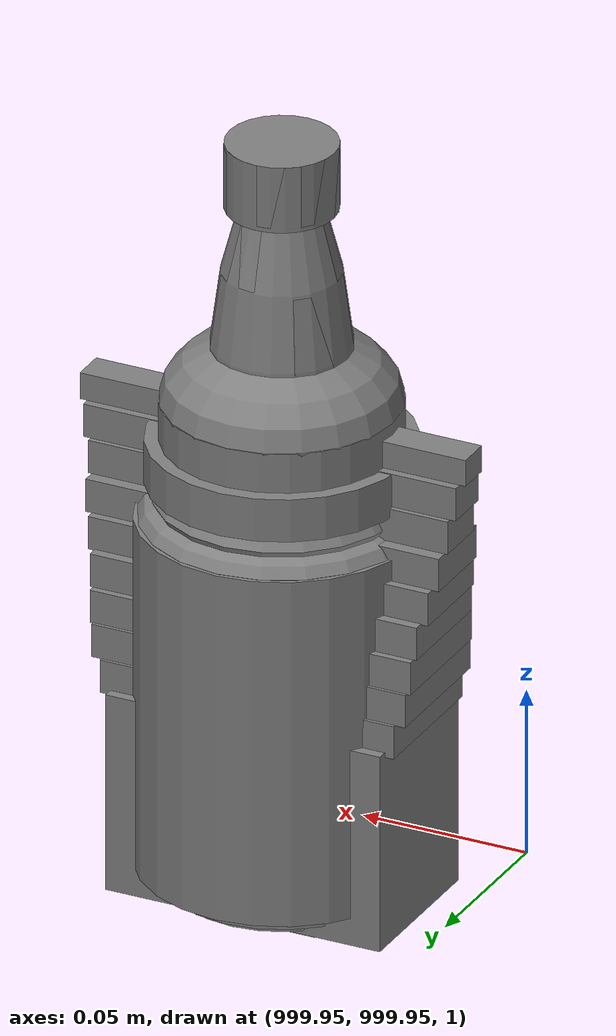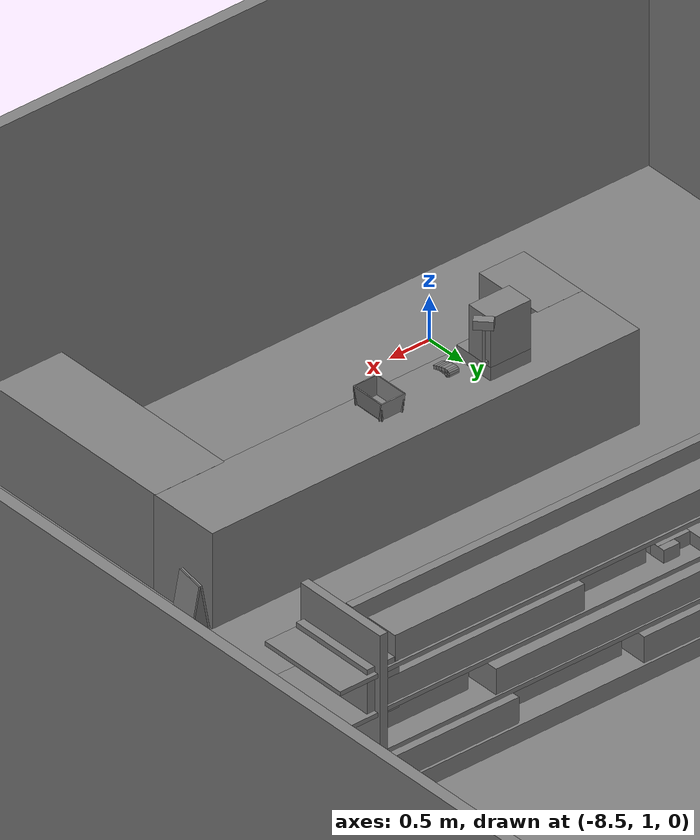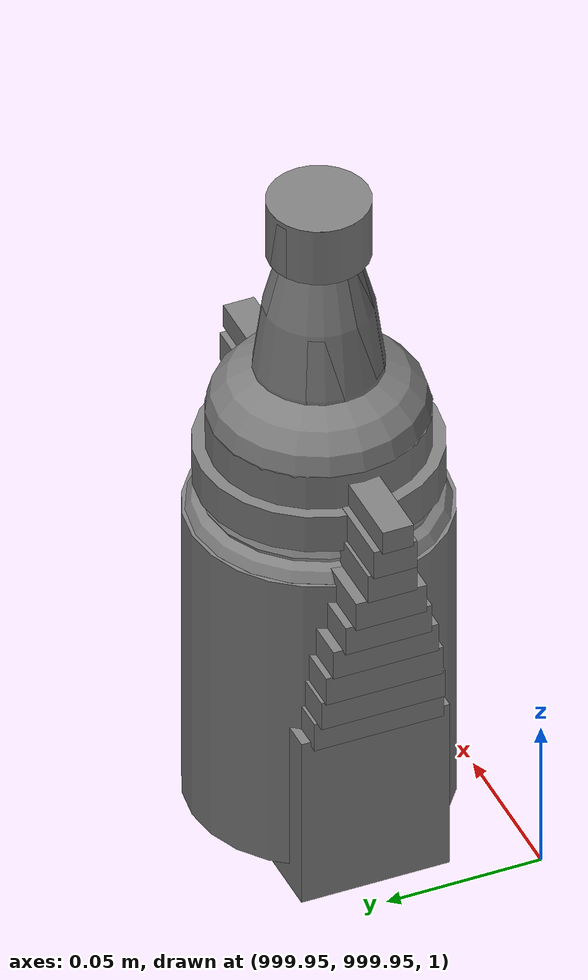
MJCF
<mujoco>
    <option gravity="0.000000000 0.000000000 -9.810000420" timestep="0.0166666" integrator="implicitfast" density="1.225" viscosity="1.8000001e-05" noslip_iterations="10" iterations="100" sdf_iterations="50">
        <flag multiccd="disable"/>
    </option>
    <size memory="1000M"/>
    <compiler coordinate="local"/>
    <worldbody>
        <light cutoff="30" pos="0 1 1" dir="0 -1 -2"/>
        <light cutoff="30" pos="0 -1 1" dir="0 1 -2"/>
        <body pos="-2.436573029 6.404376507 0.137849092" euler="0.000000000 0.000000000 0.000000000" name="openloong_gripper_2f85_fix_base_usda_shoppingtrolley_01">
            <geom contype="1" conaffinity="1" density="1000" type="box" material="" rgba="0.500000000 0.500000000 0.500000000 1.000000000" solimp="0.899999976 0.949999988 0.001000000" friction="1.000000000 0.005000000 0.000100000" solref="0.020000000 1.000000000" margin="0" condim="3" group="0" pos="-0.126757339 -0.182533979 0.598989725" quat="0.996607184 0.055331606 -0.059003651 -0.015205891" size="0.013499999 0.287999988 0.053999998" name="openloong_gripper_2f85_fix_base_usda_geom_FC31B5EF_0E04_473B_8271_D4D94ADC8D1E"/>
            <geom contype="1" conaffinity="1" density="1000" type="box" material="" rgba="0.500000000 0.500000000 0.500000000 1.000000000" solimp="0.899999976 0.949999988 0.001000000" friction="1.000000000 0.005000000 0.000100000" solref="0.020000000 1.000000000" margin="0" condim="3" group="0" pos="-0.000005364 0.100332208 0.734785020" quat="0.999668717 0.025737956 -0.000000010 0.000000000" size="0.135000005 0.019800000 0.152999997" name="openloong_gripper_2f85_fix_base_usda_geom_CF2C68D1_5255_4F70_AB92_5343DDB813B4"/>
            <geom contype="1" conaffinity="1" density="1000" type="box" material="" rgba="0.500000000 0.500000000 0.500000000 1.000000000" solimp="0.899999976 0.949999988 0.001000000" friction="1.000000000 0.005000000 0.000100000" solref="0.020000000 1.000000000" margin="0" condim="3" group="0" pos="-0.142927840 -0.199506134 0.784674108" quat="0.998421252 0.016904408 -0.027109101 -0.046199299" size="0.013499999 0.305999994 0.063000001" name="openloong_gripper_2f85_fix_base_usda_geom_298A35B7_AFC1_48F1_BD13_51F80BB15D08"/>
            <geom contype="1" conaffinity="1" density="1000" type="box" material="" rgba="0.500000000 0.500000000 0.500000000 1.000000000" solimp="0.899999976 0.949999988 0.001000000" friction="1.000000000 0.005000000 0.000100000" solref="0.020000000 1.000000000" margin="0" condim="3" group="0" pos="-0.000006008 -0.484932661 0.670727849" quat="0.997585475 0.069449045 -0.000000004 -0.000000089" size="0.179999992 0.013499999 0.170999989" name="openloong_gripper_2f85_fix_base_usda_geom_324E56CE_E7DD_492A_B2F3_A28DBF0175F9"/>
            <geom contype="1" conaffinity="1" density="1000" type="box" material="" rgba="0.500000000 0.500000000 0.500000000 1.000000000" solimp="0.899999976 0.949999988 0.001000000" friction="1.000000000 0.005000000 0.000100000" solref="0.020000000 1.000000000" margin="0" condim="3" group="0" pos="-0.000004721 -0.174527690 0.560063601" quat="0.996704638 0.081116498 -0.000000004 0.000000000" size="0.126000002 0.287999988 0.009000000" name="openloong_gripper_2f85_fix_base_usda_geom_C71A961D_8584_4099_9416_8E31265B3C52"/>
            <geom contype="1" conaffinity="1" density="1000" type="box" material="" rgba="0.500000000 0.500000000 0.500000000 1.000000000" solimp="0.899999976 0.949999988 0.001000000" friction="1.000000000 0.005000000 0.000100000" solref="0.020000000 1.000000000" margin="0" condim="3" group="0" pos="-0.012634277 -0.174527690 -0.088243507" quat="1.000000000 0.000000000 -0.000000004 0.000000000" size="0.135000005 0.287999988 0.044999998" name="openloong_gripper_2f85_fix_base_usda_geom_162D444A_924C_4A74_BDD0_4C90ED3AAE51"/>
            <geom contype="1" conaffinity="1" density="1000" type="box" material="" rgba="0.500000000 0.500000000 0.500000000 1.000000000" solimp="0.899999976 0.949999988 0.001000000" friction="1.000000000 0.005000000 0.000100000" solref="0.020000000 1.000000000" margin="0" condim="3" group="0" pos="0.131482959 -0.182533979 0.598989725" quat="0.996607125 0.055331629 0.059003670 0.015205893" size="0.013499999 0.287999988 0.053999998" name="openloong_gripper_2f85_fix_base_usda_geom_939E351E_F68E_4A37_A6F0_027D8EB8B8B4"/>
            <geom contype="1" conaffinity="1" density="1000" type="box" material="" rgba="0.500000000 0.500000000 0.500000000 1.000000000" solimp="0.899999976 0.949999988 0.001000000" friction="1.000000000 0.005000000 0.000100000" solref="0.020000000 1.000000000" margin="0" condim="3" group="0" pos="0.148195267 -0.199506566 0.782808602" quat="0.998808920 0.017156634 0.026950166 0.036880098" size="0.013499999 0.305999994 0.063000001" name="openloong_gripper_2f85_fix_base_usda_geom_664884D3_D612_4AA5_B748_8EDDFB05789A"/>
            <geom contype="1" conaffinity="1" density="1000" type="box" material="" rgba="0.500000000 0.500000000 0.500000000 1.000000000" solimp="0.899999976 0.949999988 0.001000000" friction="1.000000000 0.005000000 0.000100000" solref="0.020000000 1.000000000" margin="0" condim="3" group="0" pos="0.103667587 0.233050480 0.912927270" quat="0.634205043 -0.622199059 -0.324503720 0.324576139" size="0.017999999 0.022499999 0.035999998" name="openloong_gripper_2f85_fix_base_usda_geom_4B238FDD_809B_45B2_B20B_9A222B658D44"/>
            <geom contype="1" conaffinity="1" density="1000" type="box" material="" rgba="0.500000000 0.500000000 0.500000000 1.000000000" solimp="0.899999976 0.949999988 0.001000000" friction="1.000000000 0.005000000 0.000100000" solref="0.020000000 1.000000000" margin="0" condim="3" group="0" pos="-0.107458733 0.238907143 0.911498845" quat="0.634576976 0.622505128 -0.330067992 -0.317575932" size="0.017999999 0.022499999 0.035999998" name="openloong_gripper_2f85_fix_base_usda_geom_7BC0217C_1322_4655_9C56_3B6011B01AA9"/>
            <geom contype="1" conaffinity="1" density="1000" type="box" material="" rgba="0.500000000 0.500000000 0.500000000 1.000000000" solimp="0.899999976 0.949999988 0.001000000" friction="1.000000000 0.005000000 0.000100000" solref="0.020000000 1.000000000" margin="0" condim="3" group="0" pos="-0.169898406 -0.178061336 0.864131629" quat="0.916343808 -0.400392294 -0.000000045 0.000000030" size="0.017999999 0.022499999 0.089999996" name="openloong_gripper_2f85_fix_base_usda_geom_EE90D6A1_E1EF_4E8F_81BF_F307322BDDDD"/>
            <geom contype="1" conaffinity="1" density="1000" type="box" material="" rgba="0.500000000 0.500000000 0.500000000 1.000000000" solimp="0.899999976 0.949999988 0.001000000" friction="1.000000000 0.005000000 0.000100000" solref="0.020000000 1.000000000" margin="0" condim="3" group="0" pos="0.169898629 -0.178061336 0.864131629" quat="0.916343808 -0.400392294 -0.000000045 0.000000030" size="0.017999999 0.022499999 0.089999996" name="openloong_gripper_2f85_fix_base_usda_geom_68B905D3_EAD2_4265_A969_0CE4A89729CE"/>
            <geom contype="1" conaffinity="1" density="1000" type="box" material="" rgba="0.500000000 0.500000000 0.500000000 1.000000000" solimp="0.899999976 0.949999988 0.001000000" friction="1.000000000 0.005000000 0.000100000" solref="0.020000000 1.000000000" margin="0" condim="3" group="0" pos="-0.005004787 0.248085022 0.912686050" quat="1.000000000 0.000000000 0.000000000 0.000000000" size="0.107999995 0.022499999 0.022499999" name="openloong_gripper_2f85_fix_base_usda_geom_3AFF547A_DF70_4BFB_8D2A_AA311ECCE0B0"/>
            <geom contype="1" conaffinity="1" density="1000" type="box" material="" rgba="0.500000000 0.500000000 0.500000000 1.000000000" solimp="0.899999976 0.949999988 0.001000000" friction="1.000000000 0.005000000 0.000100000" solref="0.020000000 1.000000000" margin="0" condim="3" group="0" pos="-0.169898406 -0.043119621 0.915120542" quat="0.687021017 0.726584017 -0.005590606 -0.006832919" size="0.017999999 0.022499999 0.089999996" name="openloong_gripper_2f85_fix_base_usda_geom_D42E6EEB_62D5_4017_A88A_FBBFE8BD549B"/>
            <geom contype="1" conaffinity="1" density="1000" type="box" material="" rgba="0.500000000 0.500000000 0.500000000 1.000000000" solimp="0.899999976 0.949999988 0.001000000" friction="1.000000000 0.005000000 0.000100000" solref="0.020000000 1.000000000" margin="0" condim="3" group="0" pos="0.141839072 -0.191051379 0.702451229" quat="0.997147262 0.056065105 0.045779929 0.021407485" size="0.013499999 0.287999988 0.053999998" name="openloong_gripper_2f85_fix_base_usda_geom_259B6849_BF7D_40F1_8567_F7CF0C9AC6A2"/>
            <geom contype="1" conaffinity="1" density="1000" type="box" material="" rgba="0.500000000 0.500000000 0.500000000 1.000000000" solimp="0.899999976 0.949999988 0.001000000" friction="1.000000000 0.005000000 0.000100000" solref="0.020000000 1.000000000" margin="0" condim="3" group="0" pos="0.160832971 0.103427693 0.910528183" quat="0.711112797 -0.700149298 -0.042821646 0.047705106" size="0.017999999 0.022499999 0.071999997" name="openloong_gripper_2f85_fix_base_usda_geom_4FA35544_ECCA_4B80_BFD6_55271111405C"/>
            <geom contype="1" conaffinity="1" density="1000" type="box" material="" rgba="0.500000000 0.500000000 0.500000000 1.000000000" solimp="0.899999976 0.949999988 0.001000000" friction="1.000000000 0.005000000 0.000100000" solref="0.020000000 1.000000000" margin="0" condim="3" group="0" pos="-0.134013891 0.200098798 0.912192523" quat="0.694057047 0.679413557 -0.172947660 -0.163618833" size="0.017999999 0.022499999 0.035999998" name="openloong_gripper_2f85_fix_base_usda_geom_32B7F66B_F991_4A81_A1A4_B2BD2DD93FA3"/>
            <geom contype="1" conaffinity="1" density="1000" type="box" material="" rgba="0.500000000 0.500000000 0.500000000 1.000000000" solimp="0.899999976 0.949999988 0.001000000" friction="1.000000000 0.005000000 0.000100000" solref="0.020000000 1.000000000" margin="0" condim="3" group="0" pos="0.134013891 0.200098798 0.912192523" quat="0.692574680 -0.680924535 -0.166899428 0.169783980" size="0.017999999 0.022499999 0.035999998" name="openloong_gripper_2f85_fix_base_usda_geom_87D0B4AE_B524_47E7_8148_5B6F6EB7006C"/>
            <geom contype="1" conaffinity="1" density="1000" type="box" material="" rgba="0.500000000 0.500000000 0.500000000 1.000000000" solimp="0.899999976 0.949999988 0.001000000" friction="1.000000000 0.005000000 0.000100000" solref="0.020000000 1.000000000" margin="0" condim="3" group="0" pos="-0.160832763 0.103427693 0.910528183" quat="0.711469591 0.699786782 -0.048386075 -0.042050660" size="0.017999999 0.022499999 0.071999997" name="openloong_gripper_2f85_fix_base_usda_geom_05636387_47E3_451D_AF37_F5EC92F52ED2"/>
            <geom contype="1" conaffinity="1" density="1000" type="box" material="" rgba="0.500000000 0.500000000 0.500000000 1.000000000" solimp="0.899999976 0.949999988 0.001000000" friction="1.000000000 0.005000000 0.000100000" solref="0.020000000 1.000000000" margin="0" condim="3" group="0" pos="-0.135714188 -0.191051379 0.694841146" quat="0.997147322 0.056064609 -0.045779683 -0.021407485" size="0.013499999 0.287999988 0.053999998" name="openloong_gripper_2f85_fix_base_usda_geom_C07A40D1_DDBA_4EBF_BF08_2A825E35FC60"/>
            <geom contype="1" conaffinity="1" density="1000" type="box" material="" rgba="0.500000000 0.500000000 0.500000000 1.000000000" solimp="0.899999976 0.949999988 0.001000000" friction="1.000000000 0.005000000 0.000100000" solref="0.020000000 1.000000000" margin="0" condim="3" group="0" pos="0.169898629 -0.043119621 0.915120542" quat="0.687029123 -0.726576388 -0.006509603 0.005963952" size="0.017999999 0.022499999 0.089999996" name="openloong_gripper_2f85_fix_base_usda_geom_C90D6B4F_E11B_4CF1_998F_BFF096113EF7"/>
            <freejoint name="openloong_gripper_2f85_fix_base_usda_shoppingtrolley_01_joint"/>
            <site size="0.005000000 0.005000000 0.005000000" rgba="0.500000000 0.500000000 0.500000000 1.000000000" pos="0.000000000 0.000000000 0.000000000" quat="1.000000000 0.000000000 0.000000000 0.000000000" group="0" type="sphere" name="openloong_gripper_2f85_fix_base_usda_shoppingtrolley_01"/>
        </body>
        <body pos="-1.947732687 5.810266018 1.735279679" euler="78.922149658 72.747306824 -149.046524048" mocap="true" name="spotlight3_SpotLight"/>
        <body pos="-1.963579297 6.176063538 1.770202518" euler="-174.776870728 63.094280243 -161.834320068" mocap="true" name="spotlight1_SpotLight"/>
        <body pos="1000.000000000 1000.000000000 1.000000000" euler="0.000000000 0.000000000 0.000000000" name="openloong_gripper_2f85_fix_base_usda_jar_01">
            <geom contype="1" conaffinity="1" density="1000" type="box" material="" rgba="0.500000000 0.500000000 0.500000000 1.000000000" solimp="0.899999976 0.949999988 0.001000000" friction="1.000000000 0.005000000 0.000100000" solref="0.020000000 1.000000000" margin="0" condim="3" group="0" pos="0.000000000 0.000000000 0.006158113" quat="1.000000000 0.000000000 0.000000000 0.000000000" size="0.020000000 0.020000000 0.005000000" name="openloong_gripper_2f85_fix_base_usda_geom_2BDDCA7E_BD53_415F_911F_D42A26854D7D"/>
            <geom contype="1" conaffinity="1" density="1000" type="cylinder" material="" rgba="0.500000000 0.500000000 0.500000000 1.000000000" solimp="0.899999976 0.949999988 0.001000000" friction="1.000000000 0.005000000 0.000100000" solref="0.020000000 1.000000000" margin="0" condim="3" group="0" pos="0.000000000 0.000000000 0.062744498" quat="1.000000000 0.000000000 0.000000000 0.000000000" size="0.041000001 0.052999999 1.000000000" name="openloong_gripper_2f85_fix_base_usda_geom_BEC4721F_BA49_4E72_ADB1_FEF598DF4D8A"/>
            <geom contype="1" conaffinity="1" density="1000" type="ellipsoid" material="" rgba="0.500000000 0.500000000 0.500000000 1.000000000" solimp="0.899999976 0.949999988 0.001000000" friction="1.000000000 0.005000000 0.000100000" solref="0.020000000 1.000000000" margin="0" condim="3" group="0" pos="0.000000000 0.000000000 0.122252703" quat="1.000000000 0.000000000 0.000000000 0.000000000" size="0.035999998 0.035999998 0.010000000" name="openloong_gripper_2f85_fix_base_usda_geom_E8D37BD2_4F38_4AD0_A897_3479108504D6"/>
            <geom contype="1" conaffinity="1" density="1000" type="cylinder" material="" rgba="0.500000000 0.500000000 0.500000000 1.000000000" solimp="0.899999976 0.949999988 0.001000000" friction="1.000000000 0.005000000 0.000100000" solref="0.020000000 1.000000000" margin="0" condim="3" group="0" pos="0.000000000 0.000000000 0.015747190" quat="1.000000000 0.000000000 0.000000000 0.000000000" size="0.035000000 0.010000000 1.000000000" name="openloong_gripper_2f85_fix_base_usda_geom_751B8660_5CFA_49C4_9B44_09CB60AB63E3"/>
            <geom contype="1" conaffinity="1" density="1000" type="ellipsoid" material="" rgba="0.500000000 0.500000000 0.500000000 1.000000000" solimp="0.899999976 0.949999988 0.001000000" friction="1.000000000 0.005000000 0.000100000" solref="0.020000000 1.000000000" margin="0" condim="3" group="0" pos="0.000000000 0.000000000 0.115815401" quat="1.000000000 0.000000000 0.000000000 0.000000000" size="0.039999999 0.039999999 0.010000000" name="openloong_gripper_2f85_fix_base_usda_geom_815E247E_B035_404D_BD6B_EF7B8E2AF251"/>
            <geom contype="1" conaffinity="1" density="1000" type="cylinder" material="" rgba="0.500000000 0.500000000 0.500000000 1.000000000" solimp="0.899999976 0.949999988 0.001000000" friction="1.000000000 0.005000000 0.000100000" solref="0.020000000 1.000000000" margin="0" condim="3" group="0" pos="0.000000000 0.000000000 0.133183479" quat="1.000000000 0.000000000 0.000000000 0.000000000" size="0.037999999 0.006500000 1.000000000" name="openloong_gripper_2f85_fix_base_usda_geom_532A5013_063D_49CE_A21F_8A8A85D9CC0B"/>
            <freejoint name="openloong_gripper_2f85_fix_base_usda_jar_01_joint"/>
            <site size="0.005000000 0.005000000 0.005000000" rgba="0.500000000 0.500000000 0.500000000 1.000000000" pos="0.000000000 0.000000000 0.000000000" quat="1.000000000 0.000000000 0.000000000 0.000000000" group="0" type="sphere" name="openloong_gripper_2f85_fix_base_usda_jar_01site"/>
        </body>
        <body pos="1000.000000000 1000.000000000 1.000000000" euler="0.000000000 0.000000000 0.000000000" name="openloong_gripper_2f85_fix_base_usda_can">
            <geom contype="1" conaffinity="1" density="1000" type="cylinder" material="" rgba="0.500000000 0.500000000 0.500000000 1.000000000" solimp="0.899999976 0.949999988 0.001000000" friction="1.000000000 0.005000000 0.000100000" solref="0.020000000 1.000000000" margin="0" condim="3" group="0" pos="0.000000000 0.000000000 0.079676986" quat="1.000000000 0.000000000 0.000000000 0.000000000" size="0.034000002 0.071999997 1.000000000" name="openloong_gripper_2f85_fix_base_usda_geom_1FD17F61_4131_4F4A_8FC2_E07236788E0D"/>
            <geom contype="1" conaffinity="1" density="1000" type="ellipsoid" material="" rgba="0.500000000 0.500000000 0.500000000 1.000000000" solimp="0.899999976 0.949999988 0.001000000" friction="1.000000000 0.005000000 0.000100000" solref="0.020000000 1.000000000" margin="0" condim="3" group="0" pos="0.000000000 0.000000000 0.151854277" quat="1.000000000 0.000000000 0.000000000 0.000000000" size="0.034000002 0.034000002 0.020000000" name="openloong_gripper_2f85_fix_base_usda_geom_12FADF10_9014_4D8F_B539_DE396D54E50C"/>
            <geom contype="1" conaffinity="1" density="1000" type="box" material="" rgba="0.500000000 0.500000000 0.500000000 1.000000000" solimp="0.899999976 0.949999988 0.001000000" friction="1.000000000 0.005000000 0.000100000" solref="0.020000000 1.000000000" margin="0" condim="3" group="0" pos="0.000000000 0.000000000 0.004777670" quat="1.000000000 0.000000000 0.000000000 0.000000000" size="0.020000000 0.020000000 0.005000000" name="openloong_gripper_2f85_fix_base_usda_geom_B6A98C5C_EA64_4FC5_8BD0_7AA93C91D709"/>
            <freejoint name="openloong_gripper_2f85_fix_base_usda_can_joint"/>
            <site size="0.005000000 0.005000000 0.005000000" rgba="0.500000000 0.500000000 0.500000000 1.000000000" pos="0.000000000 0.000000000 0.000000000" quat="1.000000000 0.000000000 0.000000000 0.000000000" group="0" type="sphere" name="openloong_gripper_2f85_fix_base_usda_cansite"/>
        </body>
        <body pos="1000.000000000 1000.000000000 1.000000000" euler="0.000000000 0.000000000 0.000000000" name="openloong_gripper_2f85_fix_base_usda_salt">
            <geom contype="1" conaffinity="1" density="1000" type="box" material="" rgba="0.500000000 0.500000000 0.500000000 1.000000000" solimp="0.899999976 0.949999988 0.001000000" friction="1.000000000 0.005000000 0.000100000" solref="0.020000000 1.000000000" margin="0" condim="3" group="0" pos="0.000305176 0.000000000 0.084862232" quat="1.000000000 0.000000000 0.000000000 0.000000000" size="0.048999999 0.018999999 0.005000000" name="openloong_gripper_2f85_fix_base_usda_geom_1A9D7EF1_EAD2_4526_BC39_5A70165C20B0"/>
            <geom contype="1" conaffinity="1" density="1000" type="box" material="" rgba="0.500000000 0.500000000 0.500000000 1.000000000" solimp="0.899999976 0.949999988 0.001000000" friction="1.000000000 0.005000000 0.000100000" solref="0.020000000 1.000000000" margin="0" condim="3" group="0" pos="0.000305176 0.000000000 0.104564309" quat="1.000000000 0.000000000 0.000000000 0.000000000" size="0.052000001 0.014000000 0.005000000" name="openloong_gripper_2f85_fix_base_usda_geom_1C9A23CC_D435_435F_9A58_B50E94971D0A"/>
            <geom contype="1" conaffinity="1" density="1000" type="box" material="" rgba="0.500000000 0.500000000 0.500000000 1.000000000" solimp="0.899999976 0.949999988 0.001000000" friction="1.000000000 0.005000000 0.000100000" solref="0.020000000 1.000000000" margin="0" condim="3" group="0" pos="0.000305176 0.000000000 0.114487171" quat="1.000000000 0.000000000 0.000000000 0.000000000" size="0.054000001 0.011500000 0.005000000" name="openloong_gripper_2f85_fix_base_usda_geom_8BBE932C_1BE6_456E_9ABC_56DD665D6DC2"/>
            <geom contype="1" conaffinity="1" density="1000" type="box" material="" rgba="0.500000000 0.500000000 0.500000000 1.000000000" solimp="0.899999976 0.949999988 0.001000000" friction="1.000000000 0.005000000 0.000100000" solref="0.020000000 1.000000000" margin="0" condim="3" group="0" pos="0.000305176 0.000000000 0.075103164" quat="1.000000000 0.000000000 0.000000000 0.000000000" size="0.048000000 0.020000000 0.005000000" name="openloong_gripper_2f85_fix_base_usda_geom_D06D5555_B4C3_4C83_B877_4FFC9AA2AB39"/>
            <geom contype="1" conaffinity="1" density="1000" type="box" material="" rgba="0.500000000 0.500000000 0.500000000 1.000000000" solimp="0.899999976 0.949999988 0.001000000" friction="1.000000000 0.005000000 0.000100000" solref="0.020000000 1.000000000" margin="0" condim="3" group="0" pos="0.000305176 0.000000000 0.134892464" quat="1.000000000 0.000000000 0.000000000 0.000000000" size="0.057000000 0.007000000 0.005000000" name="openloong_gripper_2f85_fix_base_usda_geom_C39358BE_AD99_43C6_BB92_BDAF46F8631F"/>
            <geom contype="1" conaffinity="1" density="1000" type="box" material="" rgba="0.500000000 0.500000000 0.500000000 1.000000000" solimp="0.899999976 0.949999988 0.001000000" friction="1.000000000 0.005000000 0.000100000" solref="0.020000000 1.000000000" margin="0" condim="3" group="0" pos="0.000305176 0.000000000 0.094920278" quat="1.000000000 0.000000000 0.000000000 0.000000000" size="0.050000001 0.017000001 0.005000000" name="openloong_gripper_2f85_fix_base_usda_geom_C97F19BE_D089_44DA_84D3_5AB01959F93B"/>
            <geom contype="1" conaffinity="1" density="1000" type="box" material="" rgba="0.500000000 0.500000000 0.500000000 1.000000000" solimp="0.899999976 0.949999988 0.001000000" friction="1.000000000 0.005000000 0.000100000" solref="0.020000000 1.000000000" margin="0" condim="3" group="0" pos="0.000305176 0.000000000 0.065204859" quat="1.000000000 0.000000000 0.000000000 0.000000000" size="0.045000002 0.021000000 0.005000000" name="openloong_gripper_2f85_fix_base_usda_geom_4DFA7975_0BB6_4D9B_99E4_7F4D60CF6AC2"/>
            <geom contype="1" conaffinity="1" density="1000" type="box" material="" rgba="0.500000000 0.500000000 0.500000000 1.000000000" solimp="0.899999976 0.949999988 0.001000000" friction="1.000000000 0.005000000 0.000100000" solref="0.020000000 1.000000000" margin="0" condim="3" group="0" pos="0.000305176 0.000000000 0.144135714" quat="1.000000000 0.000000000 0.000000000 0.000000000" size="0.059000000 0.005000000 0.004000000" name="openloong_gripper_2f85_fix_base_usda_geom_223DB115_3EE5_48E0_8B10_A26F54E6C5B3"/>
            <geom contype="1" conaffinity="1" density="1000" type="box" material="" rgba="0.500000000 0.500000000 0.500000000 1.000000000" solimp="0.899999976 0.949999988 0.001000000" friction="1.000000000 0.005000000 0.000100000" solref="0.020000000 1.000000000" margin="0" condim="3" group="0" pos="0.000000000 0.000000000 0.031593561" quat="1.000000000 0.000000000 0.000000000 0.000000000" size="0.041999999 0.024000000 0.029999999" name="openloong_gripper_2f85_fix_base_usda_geom_57E87654_C6F0_425E_B54D_938EF474E89B"/>
            <geom contype="1" conaffinity="1" density="1000" type="box" material="" rgba="0.500000000 0.500000000 0.500000000 1.000000000" solimp="0.899999976 0.949999988 0.001000000" friction="1.000000000 0.005000000 0.000100000" solref="0.020000000 1.000000000" margin="0" condim="3" group="0" pos="0.000305176 0.000000000 0.124608755" quat="1.000000000 0.000000000 0.000000000 0.000000000" size="0.055000000 0.008000000 0.005000000" name="openloong_gripper_2f85_fix_base_usda_geom_781B9B2C_F68E_419E_BD94_8BA456AFC6B2"/>
            <freejoint name="openloong_gripper_2f85_fix_base_usda_salt_joint"/>
            <site size="0.005000000 0.005000000 0.005000000" rgba="0.500000000 0.500000000 0.500000000 1.000000000" pos="0.000000000 0.000000000 0.000000000" quat="1.000000000 0.000000000 0.000000000 0.000000000" group="0" type="sphere" name="openloong_gripper_2f85_fix_base_usda_saltsite"/>
        </body>
        <body pos="1000.000000000 1000.000000000 1.000000000" euler="0.000000000 0.000000000 0.000000000" name="openloong_gripper_2f85_fix_base_usda_bottle_red">
            <geom contype="1" conaffinity="1" density="1000" type="ellipsoid" material="" rgba="0.500000000 0.500000000 0.500000000 1.000000000" solimp="0.899999976 0.949999988 0.001000000" friction="1.000000000 0.005000000 0.000100000" solref="0.020000000 1.000000000" margin="0" condim="3" group="0" pos="0.000000000 0.000000000 0.144284487" quat="1.000000000 0.000000000 0.000000000 0.000000000" size="0.021000000 0.021000000 0.079999998" name="openloong_gripper_2f85_fix_base_usda_geom_641E3B6F_2F78_4AE6_86B3_BBAE2C5CDC8E"/>
            <geom contype="1" conaffinity="1" density="1000" type="cylinder" material="" rgba="0.500000000 0.500000000 0.500000000 1.000000000" solimp="0.899999976 0.949999988 0.001000000" friction="1.000000000 0.005000000 0.000100000" solref="0.020000000 1.000000000" margin="0" condim="3" group="0" pos="0.000000000 0.000000000 0.220618963" quat="1.000000000 0.000000000 0.000000000 0.000000000" size="0.016000001 0.010000000 1.000000000" name="openloong_gripper_2f85_fix_base_usda_geom_12115891_F4CF_466A_A637_918EEE3C973D"/>
            <geom contype="1" conaffinity="1" density="1000" type="ellipsoid" material="" rgba="0.500000000 0.500000000 0.500000000 1.000000000" solimp="0.899999976 0.949999988 0.001000000" friction="1.000000000 0.005000000 0.000100000" solref="0.020000000 1.000000000" margin="0" condim="3" group="0" pos="0.000000000 0.000000000 0.118945479" quat="1.000000000 0.000000000 0.000000000 0.000000000" size="0.030999999 0.030999999 0.029999999" name="openloong_gripper_2f85_fix_base_usda_geom_8BF9663F_4663_4EE5_A28B_E9C1EB162EEA"/>
            <geom contype="1" conaffinity="1" density="1000" type="box" material="" rgba="0.500000000 0.500000000 0.500000000 1.000000000" solimp="0.899999976 0.949999988 0.001000000" friction="1.000000000 0.005000000 0.000100000" solref="0.020000000 1.000000000" margin="0" condim="3" group="0" pos="0.000000000 0.000000000 0.002189159" quat="1.000000000 0.000000000 0.000000000 0.000000000" size="0.020000000 0.020000000 0.003000000" name="openloong_gripper_2f85_fix_base_usda_geom_70513872_9F54_4430_BE33_2E6A82CFEBEA"/>
            <geom contype="1" conaffinity="1" density="1000" type="cylinder" material="" rgba="0.500000000 0.500000000 0.500000000 1.000000000" solimp="0.899999976 0.949999988 0.001000000" friction="1.000000000 0.005000000 0.000100000" solref="0.020000000 1.000000000" margin="0" condim="3" group="0" pos="0.000000000 -0.000366211 0.060884237" quat="1.000000000 0.000000000 0.000000000 0.000000000" size="0.030999999 0.057999998 1.000000000" name="openloong_gripper_2f85_fix_base_usda_geom_A4D72E69_5C9D_4C56_B898_8FAA3AE062AE"/>
            <freejoint name="openloong_gripper_2f85_fix_base_usda_bottle_red_joint"/>
            <site size="0.005000000 0.005000000 0.005000000" rgba="0.500000000 0.500000000 0.500000000 1.000000000" pos="0.000000000 0.000000000 0.000000000" quat="0.999961913 0.008726535 0.000000000 0.000000000" group="0" type="sphere" name="openloong_gripper_2f85_fix_base_usda_bottle_redsite"/>
        </body>
        <body pos="-2.302204609 6.217363834 1.750039220" euler="97.063362122 -35.438114166 -26.854743958" mocap="true" name="spotlight5_SpotLight"/>
        <body pos="1000.000000000 1000.000000000 1.000000000" euler="0.000000000 0.000000000 0.000000000" name="openloong_gripper_2f85_fix_base_usda_bottle_blue">
            <geom contype="1" conaffinity="1" density="1000" type="ellipsoid" material="" rgba="0.500000000 0.500000000 0.500000000 1.000000000" solimp="0.899999976 0.949999988 0.001000000" friction="1.000000000 0.005000000 0.000100000" solref="0.020000000 1.000000000" margin="0" condim="3" group="0" pos="0.000000000 0.000000000 0.118920922" quat="1.000000000 0.000000000 0.000000000 0.000000000" size="0.030999999 0.030999999 0.029999999" name="openloong_gripper_2f85_fix_base_usda_geom_144F2C31_61E1_4114_823F_1E4A39F2A476"/>
            <geom contype="1" conaffinity="1" density="1000" type="box" material="" rgba="0.500000000 0.500000000 0.500000000 1.000000000" solimp="0.899999976 0.949999988 0.001000000" friction="1.000000000 0.005000000 0.000100000" solref="0.020000000 1.000000000" margin="0" condim="3" group="0" pos="0.000000000 0.000000000 0.002164602" quat="1.000000000 0.000000000 0.000000000 0.000000000" size="0.020000000 0.020000000 0.003000000" name="openloong_gripper_2f85_fix_base_usda_geom_48D1D57B_317D_44EF_B3D7_966C81AD8638"/>
            <geom contype="1" conaffinity="1" density="1000" type="cylinder" material="" rgba="0.500000000 0.500000000 0.500000000 1.000000000" solimp="0.899999976 0.949999988 0.001000000" friction="1.000000000 0.005000000 0.000100000" solref="0.020000000 1.000000000" margin="0" condim="3" group="0" pos="0.000000000 -0.000366211 0.060859680" quat="1.000000000 0.000000000 0.000000000 0.000000000" size="0.030999999 0.057999998 1.000000000" name="openloong_gripper_2f85_fix_base_usda_geom_17083748_704E_4D3F_9071_F2ACBE0584D8"/>
            <geom contype="1" conaffinity="1" density="1000" type="cylinder" material="" rgba="0.500000000 0.500000000 0.500000000 1.000000000" solimp="0.899999976 0.949999988 0.001000000" friction="1.000000000 0.005000000 0.000100000" solref="0.020000000 1.000000000" margin="0" condim="3" group="0" pos="0.000000000 0.000000000 0.220594406" quat="1.000000000 0.000000000 0.000000000 0.000000000" size="0.016000001 0.010000000 1.000000000" name="openloong_gripper_2f85_fix_base_usda_geom_C1FF5EF6_53B8_4439_9FEF_69208E452D81"/>
            <geom contype="1" conaffinity="1" density="1000" type="ellipsoid" material="" rgba="0.500000000 0.500000000 0.500000000 1.000000000" solimp="0.899999976 0.949999988 0.001000000" friction="1.000000000 0.005000000 0.000100000" solref="0.020000000 1.000000000" margin="0" condim="3" group="0" pos="0.000000000 0.000000000 0.144259930" quat="1.000000000 0.000000000 0.000000000 0.000000000" size="0.021000000 0.021000000 0.079999998" name="openloong_gripper_2f85_fix_base_usda_geom_309F61EC_613F_4075_BD3D_BBB73560AB08"/>
            <freejoint name="openloong_gripper_2f85_fix_base_usda_bottle_blue_joint"/>
            <site size="0.005000000 0.005000000 0.005000000" rgba="0.500000000 0.500000000 0.500000000 1.000000000" pos="0.000000000 0.000000000 0.000000000" quat="0.999961913 0.008726535 0.000000000 0.000000000" group="0" type="sphere" name="openloong_gripper_2f85_fix_base_usda_bottle_bluesite"/>
        </body>
        <body pos="0.000000000 0.000000000 0.000000000" euler="0.000000000 0.000000000 0.000000000" name="Interactive Objects_Interactive Objects"/>
        <body pos="0.000000000 0.000000000 0.000000000" euler="0.000000000 0.000000000 0.000000000" name=" Static Objects_ Static Objects">
            <geom contype="1" conaffinity="1" density="1000" type="box" material="" rgba="0.500000000 0.500000000 0.500000000 1.000000000" solimp="0.899999976 0.949999988 0.001000000" friction="1.000000000 0.005000000 0.000100000" solref="0.020000000 1.000000000" margin="0" condim="3" group="0" pos="-3.101639986 6.150595188 1.018643856" quat="1.000000000 0.000000000 0.000000000 0.000000000" size="0.050000001 0.579999983 1.019999981" name=" Static Objects_geom_1677D20C_FA23_4A55_8A09_EE7483495F2B"/>
            <geom contype="1" conaffinity="1" density="1000" type="box" material="" rgba="0.500000000 0.500000000 0.500000000 1.000000000" solimp="0.899999976 0.949999988 0.001000000" friction="1.000000000 0.005000000 0.000100000" solref="0.020000000 1.000000000" margin="0" condim="3" group="0" pos="-2.825197220 6.153595448 1.115278244" quat="0.707107067 0.000000000 0.000000000 0.707106471" size="0.550000012 0.239999995 0.025000000" name=" Static Objects_geom_359214EA_C2E2_431E_B3B6_9B954A3D8FCE"/>
            <geom contype="1" conaffinity="1" density="1000" type="box" material="" rgba="0.500000000 0.500000000 0.500000000 1.000000000" solimp="0.899999976 0.949999988 0.001000000" friction="1.000000000 0.005000000 0.000100000" solref="0.020000000 1.000000000" margin="0" condim="3" group="0" pos="-2.825197220 6.153595448 0.097434282" quat="0.707107067 0.000000000 0.000000000 0.707106471" size="0.550000012 0.239999995 0.098999999" name=" Static Objects_geom_BE856089_8C98_4160_86D4_EFC8DB10A958"/>
            <geom contype="1" conaffinity="1" density="1000" type="box" material="" rgba="0.500000000 0.500000000 0.500000000 1.000000000" solimp="0.899999976 0.949999988 0.001000000" friction="1.000000000 0.005000000 0.000100000" solref="0.020000000 1.000000000" margin="0" condim="3" group="0" pos="-6.293097973 6.153595448 1.114443064" quat="0.707107067 0.000000000 0.000000000 0.707106471" size="0.529999971 3.134999990 0.025000000" name=" Static Objects_geom_67EE61C4_55FA_41B4_82ED_1F3CFED900ED"/>
            <geom contype="1" conaffinity="1" density="1000" type="box" material="" rgba="0.500000000 0.500000000 0.500000000 1.000000000" solimp="0.899999976 0.949999988 0.001000000" friction="1.000000000 0.005000000 0.000100000" solref="0.020000000 1.000000000" margin="0" condim="3" group="0" pos="-6.286010742 6.153595448 0.096129179" quat="0.707107067 0.000000000 0.000000000 0.707106471" size="0.529999971 3.134999990 0.098999999" name=" Static Objects_geom_E29684A8_D13C_4FD9_B3D8_A2F08E45D5F6"/>
            <geom contype="1" conaffinity="1" density="1000" type="box" material="" rgba="0.500000000 0.500000000 0.500000000 1.000000000" solimp="0.899999976 0.949999988 0.001000000" friction="1.000000000 0.005000000 0.000100000" solref="0.020000000 1.000000000" margin="0" condim="3" group="0" pos="-2.825197220 6.153595448 1.563861728" quat="0.707107067 0.000000000 0.000000000 0.707106471" size="0.550000012 0.239999995 0.025000000" name=" Static Objects_geom_EDA2369D_CD14_49E7_ACD9_3E96C113AA61"/>
            <geom contype="1" conaffinity="1" density="1000" type="box" material="" rgba="0.500000000 0.500000000 0.500000000 1.000000000" solimp="0.899999976 0.949999988 0.001000000" friction="1.000000000 0.005000000 0.000100000" solref="0.020000000 1.000000000" margin="0" condim="3" group="0" pos="-6.311686516 6.153595448 1.018643856" quat="0.707107067 0.000000000 0.000000000 0.707106471" size="0.050000001 3.150000095 1.019999981" name=" Static Objects_geom_AA800169_F9F8_4460_BC59_856796CEC03F"/>
            <geom contype="1" conaffinity="1" density="1000" type="box" material="" rgba="0.500000000 0.500000000 0.500000000 1.000000000" solimp="0.899999976 0.949999988 0.001000000" friction="1.000000000 0.005000000 0.000100000" solref="0.020000000 1.000000000" margin="0" condim="3" group="0" pos="-2.825197220 6.153595448 0.629031777" quat="0.707107067 0.000000000 0.000000000 0.707106471" size="0.550000012 0.239999995 0.025000000" name=" Static Objects_geom_612EC6AA_9F2E_4D57_934D_5E1263B2A270"/>
            <geom contype="1" conaffinity="1" density="1000" type="box" material="" rgba="0.500000000 0.500000000 0.500000000 1.000000000" solimp="0.899999976 0.949999988 0.001000000" friction="1.000000000 0.005000000 0.000100000" solref="0.020000000 1.000000000" margin="0" condim="3" group="0" pos="-6.286010742 6.153595448 1.563861728" quat="0.707107067 0.000000000 0.000000000 0.707106471" size="0.529999971 3.134999990 0.025000000" name=" Static Objects_geom_1145309A_2819_4FE5_B449_431BA4442993"/>
            <geom contype="1" conaffinity="1" density="1000" type="box" material="" rgba="0.500000000 0.500000000 0.500000000 1.000000000" solimp="0.899999976 0.949999988 0.001000000" friction="1.000000000 0.005000000 0.000100000" solref="0.020000000 1.000000000" margin="0" condim="3" group="0" pos="-6.286010742 6.153595448 0.629031777" quat="0.707107067 0.000000000 0.000000000 0.707106471" size="0.529999971 3.134999990 0.025000000" name=" Static Objects_geom_0AC147FE_C59A_47A0_A13E_0C5F09CFFACF"/>
            <geom contype="1" conaffinity="1" density="1000" type="box" material="" rgba="0.500000000 0.500000000 0.500000000 1.000000000" solimp="0.899999976 0.949999988 0.001000000" friction="1.000000000 0.005000000 0.000100000" solref="0.020000000 1.000000000" margin="0" condim="3" group="0" pos="-3.157672644 6.136868477 1.348373055" quat="1.000000000 0.000000000 0.000000000 0.000000000" size="0.200000003 0.519999981 0.300000012" name=" Static Objects_geom_2AFBDC53_8277_4BC4_B880_B0D837C93057"/>
            <geom contype="1" conaffinity="1" density="1000" type="box" material="" rgba="0.500000000 0.500000000 0.500000000 1.000000000" solimp="0.899999976 0.949999988 0.001000000" friction="1.000000000 0.005000000 0.000100000" solref="0.020000000 1.000000000" margin="0" condim="3" group="0" pos="-7.719123363 2.867671013 1.173410416" quat="1.000000000 0.000000000 0.000000000 0.000000000" size="0.250000000 0.250000000 0.079999998" name=" Static Objects_geom_4F9EA06B_84AA_430D_9954_69FDC88BEB18"/>
            <geom contype="1" conaffinity="1" density="1000" type="box" material="" rgba="0.500000000 0.500000000 0.500000000 1.000000000" solimp="0.899999976 0.949999988 0.001000000" friction="1.000000000 0.005000000 0.000100000" solref="0.020000000 1.000000000" margin="0" condim="3" group="0" pos="-7.408766270 3.088089943 1.776644945" quat="0.928051054 0.000000000 0.000000000 0.372453064" size="0.050000001 0.100000001 0.050000001" name=" Static Objects_geom_F3D63947_FB78_446F_8327_653CE0FF33BD"/>
            <geom contype="1" conaffinity="1" density="1000" type="box" material="" rgba="0.500000000 0.500000000 0.500000000 1.000000000" solimp="0.899999976 0.949999988 0.001000000" friction="1.000000000 0.005000000 0.000100000" solref="0.020000000 1.000000000" margin="0" condim="3" group="0" pos="-7.719123363 2.958004713 1.530241251" quat="1.000000000 0.000000000 0.000000000 0.000000000" size="0.250000000 0.159999996 0.280000001" name=" Static Objects_geom_9FD49CEB_AF12_4C4D_BE94_3B82853AF2C4"/>
            <geom contype="1" conaffinity="1" density="1000" type="cylinder" material="" rgba="0.500000000 0.500000000 0.500000000 1.000000000" solimp="0.899999976 0.949999988 0.001000000" friction="1.000000000 0.005000000 0.000100000" solref="0.020000000 1.000000000" margin="0" condim="3" group="0" pos="-7.427312374 3.069516420 1.502544641" quat="0.928051054 0.000000000 0.000000000 0.372453064" size="0.015000000 0.230000004 0.100000001" name=" Static Objects_geom_78079823_1FFB_424B_B8FD_3B3361919C62"/>
            <geom contype="1" conaffinity="1" density="1000" type="box" material="" rgba="0.500000000 0.500000000 0.500000000 1.000000000" solimp="0.899999976 0.949999988 0.001000000" friction="1.000000000 0.005000000 0.000100000" solref="0.020000000 1.000000000" margin="0" condim="3" group="0" pos="-7.437745571 3.067511320 1.289965630" quat="1.000000000 0.000000000 0.000000000 0.000000000" size="0.029999999 0.020000000 0.020000000" name=" Static Objects_geom_24F58210_A71E_4614_B559_D5BFC1445C46"/>
            <geom contype="1" conaffinity="1" density="1000" type="box" material="" rgba="0.500000000 0.500000000 0.500000000 1.000000000" solimp="0.899999976 0.949999988 0.001000000" friction="1.000000000 0.005000000 0.000100000" solref="0.020000000 1.000000000" margin="0" condim="3" group="0" pos="-9.058088303 6.434794426 1.209077358" quat="1.000000000 0.000000000 0.000000000 0.000000000" size="0.250000000 0.100000001 0.070000000" name=" Static Objects_geom_70F97002_7294_4EEE_A1EA_44284FB2CA99"/>
            <geom contype="1" conaffinity="1" density="1000" type="box" material="" rgba="0.500000000 0.500000000 0.500000000 1.000000000" solimp="0.899999976 0.949999988 0.001000000" friction="1.000000000 0.005000000 0.000100000" solref="0.020000000 1.000000000" margin="0" condim="3" group="0" pos="-7.886891365 6.459744930 0.352518857" quat="1.000000000 0.000000000 0.000000000 0.000000000" size="1.500000000 0.200000003 0.150000006" name=" Static Objects_geom_18FFBFD8_C9B6_4131_A39A_1FA740E53B57"/>
            <geom contype="1" conaffinity="1" density="1000" type="box" material="" rgba="0.500000000 0.500000000 0.500000000 1.000000000" solimp="0.899999976 0.949999988 0.001000000" friction="1.000000000 0.005000000 0.000100000" solref="0.020000000 1.000000000" margin="0" condim="3" group="0" pos="-9.237723351 6.464855671 1.209077358" quat="1.000000000 0.000000000 0.000000000 0.000000000" size="0.100000001 0.100000001 0.070000000" name=" Static Objects_geom_4D488F5B_B7E7_402B_8E49_4E6A61AA5CF9"/>
            <geom contype="1" conaffinity="1" density="1000" type="box" material="" rgba="0.500000000 0.500000000 0.500000000 1.000000000" solimp="0.899999976 0.949999988 0.001000000" friction="1.000000000 0.005000000 0.000100000" solref="0.020000000 1.000000000" margin="0" condim="3" group="0" pos="-6.924745083 6.362090111 1.214329123" quat="1.000000000 0.000000000 0.000000000 0.000000000" size="0.200000003 0.100000001 0.075000003" name=" Static Objects_geom_FBB043F4_193B_4360_9AAE_F0FF29269656"/>
            <geom contype="1" conaffinity="1" density="1000" type="box" material="" rgba="0.500000000 0.500000000 0.500000000 1.000000000" solimp="0.899999976 0.949999988 0.001000000" friction="1.000000000 0.005000000 0.000100000" solref="0.020000000 1.000000000" margin="0" condim="3" group="0" pos="-4.407354832 6.459744930 1.292199373" quat="1.000000000 0.000000000 0.000000000 0.000000000" size="1.240000010 0.200000003 0.150000006" name=" Static Objects_geom_A7F452BF_BAC1_4B1A_A59D_ADD028414B17"/>
            <geom contype="1" conaffinity="1" density="1000" type="box" material="" rgba="0.500000000 0.500000000 0.500000000 1.000000000" solimp="0.899999976 0.949999988 0.001000000" friction="1.000000000 0.005000000 0.000100000" solref="0.020000000 1.000000000" margin="0" condim="3" group="0" pos="-5.611940861 6.318420410 0.350975692" quat="1.000000000 0.000000000 0.000000000 0.000000000" size="0.699999988 0.100000001 0.150000006" name=" Static Objects_geom_FA3DA29A_B824_4E8E_A6E5_8DD6C3BD5FDE"/>
            <geom contype="1" conaffinity="1" density="1000" type="box" material="" rgba="0.500000000 0.500000000 0.500000000 1.000000000" solimp="0.899999976 0.949999988 0.001000000" friction="1.000000000 0.005000000 0.000100000" solref="0.020000000 1.000000000" margin="0" condim="3" group="0" pos="-6.300771236 6.459744930 1.744376063" quat="1.000000000 0.000000000 0.000000000 0.000000000" size="3.000000000 0.200000003 0.150000006" name=" Static Objects_geom_3E374404_43BE_49ED_A174_164088A96EED"/>
            <geom contype="1" conaffinity="1" density="1000" type="box" material="" rgba="0.500000000 0.500000000 0.500000000 1.000000000" solimp="0.899999976 0.949999988 0.001000000" friction="1.000000000 0.005000000 0.000100000" solref="0.020000000 1.000000000" margin="0" condim="3" group="0" pos="-6.751636982 6.459744930 0.800981164" quat="1.000000000 0.000000000 0.000000000 0.000000000" size="2.200000048 0.200000003 0.150000006" name=" Static Objects_geom_BE81326A_18AE_47B2_857F_06698388A1BA"/>
            <geom contype="1" conaffinity="1" density="1000" type="box" material="" rgba="0.500000000 0.500000000 0.500000000 1.000000000" solimp="0.899999976 0.949999988 0.001000000" friction="1.000000000 0.005000000 0.000100000" solref="0.020000000 1.000000000" margin="0" condim="3" group="0" pos="-8.844120979 6.464855671 1.209077358" quat="1.000000000 0.000000000 0.000000000 0.000000000" size="0.100000001 0.100000001 0.070000000" name=" Static Objects_geom_759BAE4B_4616_4747_AB2B_074B8D14A235"/>
            <geom contype="1" conaffinity="1" density="1000" type="box" material="" rgba="0.500000000 0.500000000 0.500000000 1.000000000" solimp="0.899999976 0.949999988 0.001000000" friction="1.000000000 0.005000000 0.000100000" solref="0.020000000 1.000000000" margin="0" condim="3" group="0" pos="-6.098561764 6.327973843 1.292199373" quat="1.000000000 0.000000000 0.000000000 0.000000000" size="0.500000000 0.100000001 0.150000006" name=" Static Objects_geom_1882F795_DD10_4258_B4FE_7861EB224530"/>
            <geom contype="1" conaffinity="1" density="1000" type="box" material="" rgba="0.500000000 0.500000000 0.500000000 1.000000000" solimp="0.899999976 0.949999988 0.001000000" friction="1.000000000 0.005000000 0.000100000" solref="0.020000000 1.000000000" margin="0" condim="3" group="0" pos="-6.824534416 6.447464466 1.212718010" quat="1.000000000 0.000000000 0.000000000 0.000000000" size="0.100000001 0.100000001 0.075000003" name=" Static Objects_geom_EA7AC348_5C60_4466_9D4E_7866585BC082"/>
            <geom contype="1" conaffinity="1" density="1000" type="box" material="" rgba="0.500000000 0.500000000 0.500000000 1.000000000" solimp="0.899999976 0.949999988 0.001000000" friction="1.000000000 0.005000000 0.000100000" solref="0.020000000 1.000000000" margin="0" condim="3" group="0" pos="-3.907610416 6.318625927 0.800981164" quat="1.000000000 0.000000000 0.000000000 0.000000000" size="0.500000000 0.100000001 0.150000006" name=" Static Objects_geom_F7DAED92_3159_46D0_BF05_F76BF25C10A7"/>
            <geom contype="1" conaffinity="1" density="1000" type="box" material="" rgba="0.500000000 0.500000000 0.500000000 1.000000000" solimp="0.899999976 0.949999988 0.001000000" friction="1.000000000 0.005000000 0.000100000" solref="0.020000000 1.000000000" margin="0" condim="3" group="0" pos="-7.373087406 6.458900928 1.214329123" quat="1.000000000 0.000000000 0.000000000 0.000000000" size="0.250000000 0.200000003 0.075000003" name=" Static Objects_geom_0B3214D0_F8A9_4924_8598_D7AC4DC84FB0"/>
            <geom contype="1" conaffinity="1" density="1000" type="box" material="" rgba="0.500000000 0.500000000 0.500000000 1.000000000" solimp="0.899999976 0.949999988 0.001000000" friction="1.000000000 0.005000000 0.000100000" solref="0.020000000 1.000000000" margin="0" condim="3" group="0" pos="-4.035642624 6.459744930 0.352518857" quat="1.000000000 0.000000000 0.000000000 0.000000000" size="0.800000012 0.200000003 0.150000006" name=" Static Objects_geom_08BBCCE7_690A_40C8_8342_5F5EF7078336"/>
            <geom contype="1" conaffinity="1" density="1000" type="box" material="" rgba="0.500000000 0.500000000 0.500000000 1.000000000" solimp="0.899999976 0.949999988 0.001000000" friction="1.000000000 0.005000000 0.000100000" solref="0.020000000 1.000000000" margin="0" condim="3" group="0" pos="-6.460197449 2.937205315 0.548931718" quat="1.000000000 0.000000000 0.000000000 0.000000000" size="2.650000095 0.430000007 0.550000012" name=" Static Objects_geom_EFBE06AD_156D_40BE_B851_387253DE431C"/>
            <geom contype="1" conaffinity="1" density="1000" type="box" material="" rgba="0.500000000 0.500000000 0.500000000 1.000000000" solimp="0.899999976 0.949999988 0.001000000" friction="1.000000000 0.005000000 0.000100000" solref="0.020000000 1.000000000" margin="0" condim="3" group="0" pos="-4.240264893 1.327049494 0.549888909" quat="1.000000000 0.000000000 0.000000000 0.000000000" size="0.430000007 1.200000048 0.550000012" name=" Static Objects_geom_92D14BBE_30F5_4E81_AD0E_5F2A728ACF68"/>
            <geom contype="1" conaffinity="1" density="1000" type="box" material="" rgba="0.500000000 0.500000000 0.500000000 1.000000000" solimp="0.899999976 0.949999988 0.001000000" friction="1.000000000 0.005000000 0.000100000" solref="0.020000000 1.000000000" margin="0" condim="3" group="0" pos="-8.830721855 2.096410990 0.549305558" quat="1.000000000 0.000000000 0.000000000 0.000000000" size="0.280000001 0.430000007 0.550000012" name=" Static Objects_geom_FEC91435_4322_4493_9C93_1242C9ACEA8F"/>
            <geom contype="1" conaffinity="1" density="1000" type="plane" material="" rgba="0.500000000 0.500000000 0.500000000 1.000000000" solimp="0.899999976 0.949999988 0.001000000" friction="1.000000000 0.005000000 0.000100000" solref="0.020000000 1.000000000" margin="0" condim="3" group="0" pos="-6.000000000 10.399999619 0.000000000" quat="1.000000000 0.000000000 0.000000000 0.000000000" size="6.050000191 10.800000191 0.010000000" name=" Static Objects_geom_54A23C7D_306C_45BF_BAF8_1DE13893F509"/>
            <geom contype="1" conaffinity="1" density="1000" type="box" material="" rgba="0.500000000 0.500000000 0.500000000 1.000000000" solimp="0.899999976 0.949999988 0.001000000" friction="1.000000000 0.005000000 0.000100000" solref="0.020000000 1.000000000" margin="0" condim="3" group="0" pos="-6.000000000 0.035000000 2.000000000" quat="1.000000000 0.000000000 0.000000000 0.000000000" size="6.079999924 0.070000000 2.000000000" name=" Static Objects_geom_1465E967_FCE2_46BC_9782_138986EFE91C"/>
            <geom contype="1" conaffinity="1" density="1000" type="box" material="" rgba="0.500000000 0.500000000 0.500000000 1.000000000" solimp="0.899999976 0.949999988 0.001000000" friction="1.000000000 0.005000000 0.000100000" solref="0.020000000 1.000000000" margin="0" condim="3" group="0" pos="-6.000000000 20.159999847 2.000000000" quat="1.000000000 0.000000000 0.000000000 0.000000000" size="6.079999924 0.070000000 2.000000000" name=" Static Objects_geom_85629BE7_8AD8_4319_8913_6035708CC149"/>
            <geom contype="1" conaffinity="1" density="1000" type="box" material="" rgba="0.500000000 0.500000000 0.500000000 1.000000000" solimp="0.899999976 0.949999988 0.001000000" friction="1.000000000 0.005000000 0.000100000" solref="0.020000000 1.000000000" margin="0" condim="3" group="0" pos="0.000000000 10.000000000 2.000000000" quat="1.000000000 0.000000000 0.000000000 0.000000000" size="0.070000000 10.500000000 2.000000000" name=" Static Objects_geom_09CDF606_75DE_4658_97FB_CCF8A0608D50"/>
            <geom contype="1" conaffinity="1" density="1000" type="box" material="" rgba="0.500000000 0.500000000 0.500000000 1.000000000" solimp="0.899999976 0.949999988 0.001000000" friction="1.000000000 0.005000000 0.000100000" solref="0.020000000 1.000000000" margin="0" condim="3" group="0" pos="-12.050000191 10.000000000 2.000000000" quat="1.000000000 0.000000000 0.000000000 0.000000000" size="0.070000000 10.500000000 2.000000000" name=" Static Objects_geom_92C18630_F070_4FBC_A0DC_622455C14D2A"/>
        </body>
        <body pos="-3.510578632 3.403555870 -0.000000100" euler="0.000000000 0.000000000 40.200675964" name="openloong_gripper_2f85_fix_base_usda_PZ">
            <geom contype="1" conaffinity="1" density="1000" type="box" material="" rgba="0.500000000 0.500000000 0.500000000 1.000000000" solimp="0.899999976 0.949999988 0.001000000" friction="1.000000000 0.005000000 0.000100000" solref="0.020000000 1.000000000" margin="0" condim="3" group="0" pos="-0.047453165 0.056484699 0.373715430" quat="0.934750080 0.077914521 0.028795123 0.345459938" size="0.180000007 0.010000000 0.379999995" name="openloong_gripper_2f85_fix_base_usda_geom_ABAFEE17_AF1F_401C_9ED3_688711EE1E4D"/>
            <geom contype="1" conaffinity="1" density="1000" type="box" material="" rgba="0.500000000 0.500000000 0.500000000 1.000000000" solimp="0.899999976 0.949999988 0.001000000" friction="1.000000000 0.005000000 0.000100000" solref="0.020000000 1.000000000" margin="0" condim="3" group="0" pos="0.047452450 -0.054376602 0.374072611" quat="0.934387863 -0.082143910 -0.030358355 0.345326364" size="0.180000007 0.010000000 0.379999995" name="openloong_gripper_2f85_fix_base_usda_geom_8B518C7D_02FE_4818_8292_D57946CC5800"/>
            <freejoint name="openloong_gripper_2f85_fix_base_usda_PZ"/>
        </body>
        <body pos="-6.332345009 2.779978037 1.034067392" euler="0.000000000 0.000000000 0.000000000" name="openloong_gripper_2f85_fix_base_usda_basket">
            <geom contype="1" conaffinity="1" density="100000" type="box" material="" rgba="0.500000000 0.500000000 0.500000000 1.000000000" solimp="0.899999976 0.949999988 0.001000000" friction="1.000000000 0.899999976 0.000100000" solref="0.020000000 1.000000000" margin="0" condim="3" group="0" pos="-0.172339439 0.000000000 0.168361664" quat="0.706172407 -0.036353018 -0.036353093 0.706170976" size="0.200000003 0.006000000 0.108000003" name="openloong_gripper_2f85_fix_base_usda_geom_ADD6A53B_22BB_4C6F_B57E_2D5290250BC4"/>
            <geom contype="1" conaffinity="1" density="100000" type="box" material="" rgba="0.500000000 0.500000000 0.500000000 1.000000000" solimp="0.899999976 0.949999988 0.001000000" friction="1.000000000 0.899999976 0.000100000" solref="0.020000000 1.000000000" margin="0" condim="3" group="0" pos="-0.039724827 -0.188568115 0.167089701" quat="0.997537494 0.070135131 0.000000000 0.000000000" size="0.150000006 0.006000000 0.108000003" name="openloong_gripper_2f85_fix_base_usda_geom_E57C6857_BCCC_426D_B57F_7A072E71B2DE"/>
            <geom contype="1" conaffinity="1" density="100000" type="box" material="" rgba="0.500000000 0.500000000 0.500000000 1.000000000" solimp="0.899999976 0.949999988 0.001000000" friction="1.000000000 0.899999976 0.000100000" solref="0.020000000 1.000000000" margin="0" condim="3" group="0" pos="-0.039724827 0.188377380 0.167089701" quat="0.997489929 -0.070808925 0.000000000 0.000000000" size="0.150000006 0.006000000 0.108000003" name="openloong_gripper_2f85_fix_base_usda_geom_2B5391AB_75EE_48B6_A10D_95A2638144CE"/>
            <geom contype="1" conaffinity="1" density="100000" type="box" material="" rgba="0.500000000 0.500000000 0.500000000 1.000000000" solimp="0.899999976 0.949999988 0.001000000" friction="1.000000000 0.899999976 0.000100000" solref="0.020000000 1.000000000" margin="0" condim="3" group="0" pos="0.094372749 0.000000000 0.168361664" quat="0.706172049 0.036353335 0.036353379 0.706171215" size="0.200000003 0.006000000 0.108000003" name="openloong_gripper_2f85_fix_base_usda_geom_CD9B97BD_16B7_4D10_BA24_7A0BD6D1E420"/>
            <geom contype="1" conaffinity="1" density="100000" type="box" material="" rgba="0.500000000 0.500000000 0.500000000 1.000000000" solimp="0.899999976 0.949999988 0.001000000" friction="1.000000000 0.899999976 0.000100000" solref="0.020000000 1.000000000" margin="0" condim="3" group="0" pos="-0.039724827 0.000000000 0.068126202" quat="1.000000000 0.000000000 0.000000000 0.000000000" size="0.129999995 0.174999997 0.006000000" name="openloong_gripper_2f85_fix_base_usda_geom_98CF6F93_6B0B_4782_BE09_997AA2F2DCA4"/>
            <freejoint name="openloong_gripper_2f85_fix_base_usda_basket_joint"/>
            <site size="0.005000000 0.005000000 0.005000000" rgba="0.500000000 0.500000000 0.500000000 1.000000000" pos="0.000000000 0.000000000 0.000000000" quat="1.000000000 0.000000000 0.000000000 0.000000000" group="0" type="sphere" name="openloong_gripper_2f85_fix_base_usda_basketsite"/>
        </body>
        <body pos="-7.168000221 2.823999882 1.227496982" euler="-0.283413976 0.056829724 -0.133293271" name="openloong_gripper_2f85_fix_base_usda_Pos">
            <geom contype="1" conaffinity="1" density="1000" type="box" material="" rgba="0.500000000 0.500000000 0.500000000 1.000000000" solimp="0.899999976 0.949999988 0.001000000" friction="1.000000000 0.005000000 0.000100000" solref="0.020000000 1.000000000" margin="0" condim="3" group="0" pos="-0.002278805 0.074524641 -0.004134059" quat="0.315989345 0.948763072 -0.000000000 0.000000000" size="0.059999999 0.013000000 0.035000000" name="openloong_gripper_2f85_fix_base_usda_geom_3352B103_0514_432F_98BC_842251DAD7F8"/>
            <geom contype="1" conaffinity="1" density="1000" type="box" material="" rgba="0.500000000 0.500000000 0.500000000 1.000000000" solimp="0.899999976 0.949999988 0.001000000" friction="1.000000000 0.005000000 0.000100000" solref="0.020000000 1.000000000" margin="0" condim="3" group="0" pos="-0.002278805 0.078031301 0.008128285" quat="0.990447521 -0.137893379 -0.000000000 -0.000000000" size="0.059999999 0.010000000 0.035000000" name="openloong_gripper_2f85_fix_base_usda_geom_168130AB_47B1_4B32_803C_20927A1C9590"/>
            <geom contype="1" conaffinity="1" density="1000" type="box" material="" rgba="0.500000000 0.500000000 0.500000000 1.000000000" solimp="0.899999976 0.949999988 0.001000000" friction="1.000000000 0.005000000 0.000100000" solref="0.020000000 1.000000000" margin="0" condim="3" group="0" pos="-0.002278805 0.080785275 -0.002596974" quat="0.287325472 -0.957833409 0.000000000 -0.000000000" size="0.059999999 0.013000000 0.035000000" name="openloong_gripper_2f85_fix_base_usda_geom_757FFEB2_2C6B_4478_8717_59157D3192AB"/>
            <geom contype="1" conaffinity="1" density="1000" type="box" material="" rgba="0.500000000 0.500000000 0.500000000 1.000000000" solimp="0.899999976 0.949999988 0.001000000" friction="1.000000000 0.005000000 0.000100000" solref="0.020000000 1.000000000" margin="0" condim="3" group="0" pos="-0.002278805 -0.098804474 -0.020146966" quat="0.988851666 0.148906454 0.000000000 -0.000000000" size="0.059999999 0.022000000 0.020000000" name="openloong_gripper_2f85_fix_base_usda_geom_1E8B7A06_5AFC_4D39_A6CD_9A477031CE8B"/>
            <geom contype="1" conaffinity="1" density="1000" type="box" material="" rgba="0.500000000 0.500000000 0.500000000 1.000000000" solimp="0.899999976 0.949999988 0.001000000" friction="1.000000000 0.005000000 0.000100000" solref="0.020000000 1.000000000" margin="0" condim="3" group="0" pos="-0.002279282 0.019920111 0.012102962" quat="0.995421767 0.095583342 -0.000000000 -0.000000000" size="0.059999999 0.025000000 0.026000001" name="openloong_gripper_2f85_fix_base_usda_geom_249F21E0_7E29_4163_9553_A2678F833D08"/>
            <geom contype="1" conaffinity="1" density="1000" type="box" material="" rgba="0.500000000 0.500000000 0.500000000 1.000000000" solimp="0.899999976 0.949999988 0.001000000" friction="1.000000000 0.005000000 0.000100000" solref="0.020000000 1.000000000" margin="0" condim="3" group="0" pos="-0.002279282 0.005734444 -0.014276862" quat="0.999571741 -0.029275302 -0.000000000 -0.000000000" size="0.059999999 0.050000001 0.010000000" name="openloong_gripper_2f85_fix_base_usda_geom_2BF71EEE_60E8_438F_9B04_15FB736BAFD6"/>
            <geom contype="1" conaffinity="1" density="1000" type="box" material="" rgba="0.500000000 0.500000000 0.500000000 1.000000000" solimp="0.899999976 0.949999988 0.001000000" friction="1.000000000 0.005000000 0.000100000" solref="0.020000000 1.000000000" margin="0" condim="3" group="0" pos="-0.002278805 0.079460382 0.007771969" quat="0.922590554 -0.385781586 0.000000000 -0.000000000" size="0.059999999 0.010000000 0.035000000" name="openloong_gripper_2f85_fix_base_usda_geom_78FCB58A_8D4D_4A25_A899_29C30672B55A"/>
            <geom contype="1" conaffinity="1" density="1000" type="box" material="" rgba="0.500000000 0.500000000 0.500000000 1.000000000" solimp="0.899999976 0.949999988 0.001000000" friction="1.000000000 0.005000000 0.000100000" solref="0.020000000 1.000000000" margin="0" condim="3" group="0" pos="-0.002279282 0.081384182 -0.001320124" quat="0.590483785 -0.807049930 0.000000000 -0.000000000" size="0.059999999 0.013000000 0.035000000" name="openloong_gripper_2f85_fix_base_usda_geom_473D4170_6060_4A68_BF46_F7211E1DCC2C"/>
            <geom contype="1" conaffinity="1" density="1000" type="box" material="" rgba="0.500000000 0.500000000 0.500000000 1.000000000" solimp="0.899999976 0.949999988 0.001000000" friction="1.000000000 0.005000000 0.000100000" solref="0.020000000 1.000000000" margin="0" condim="3" group="0" pos="-0.002278805 -0.059297800 -0.007972836" quat="0.988851666 0.148906454 0.000000000 -0.000000000" size="0.059999999 0.020000000 0.022000000" name="openloong_gripper_2f85_fix_base_usda_geom_9262DF04_FB78_4B95_8468_C05D570EE56D"/>
            <geom contype="1" conaffinity="1" density="1000" type="box" material="" rgba="0.500000000 0.500000000 0.500000000 1.000000000" solimp="0.899999976 0.949999988 0.001000000" friction="1.000000000 0.005000000 0.000100000" solref="0.020000000 1.000000000" margin="0" condim="3" group="0" pos="-0.002278805 0.076618671 -0.004656792" quat="0.004634961 0.999989629 -0.000000000 0.000000000" size="0.059999999 0.013000000 0.035000000" name="openloong_gripper_2f85_fix_base_usda_geom_F05B65E2_EFD7_417F_B288_C74A9EC019AF"/>
            <geom contype="1" conaffinity="1" density="1000" type="box" material="" rgba="0.500000000 0.500000000 0.500000000 1.000000000" solimp="0.899999976 0.949999988 0.001000000" friction="1.000000000 0.005000000 0.000100000" solref="0.020000000 1.000000000" margin="0" condim="3" group="0" pos="-0.002279282 -0.021952629 0.002960086" quat="0.991270423 0.131847665 -0.000000000 0.000000000" size="0.059999999 0.020000000 0.024000000" name="openloong_gripper_2f85_fix_base_usda_geom_EB315BC9_AD33_4AAE_AB79_5B224C4DFBCA"/>
            <geom contype="1" conaffinity="1" density="1000" type="box" material="" rgba="0.500000000 0.500000000 0.500000000 1.000000000" solimp="0.899999976 0.949999988 0.001000000" friction="1.000000000 0.005000000 0.000100000" solref="0.020000000 1.000000000" margin="0" condim="3" group="0" pos="-0.002278805 0.081418991 0.002587914" quat="0.803492308 -0.595315695 0.000000000 -0.000000000" size="0.059999999 0.013000000 0.035000000" name="openloong_gripper_2f85_fix_base_usda_geom_C265A650_B641_4907_8B26_72DF2313C39B"/>
            <geom contype="1" conaffinity="1" density="1000" type="box" material="" rgba="0.500000000 0.500000000 0.500000000 1.000000000" solimp="0.899999976 0.949999988 0.001000000" friction="1.000000000 0.005000000 0.000100000" solref="0.020000000 1.000000000" margin="0" condim="3" group="0" pos="-0.002278805 0.061115503 0.008545756" quat="0.999326169 0.036714450 0.000000000 -0.000000000" size="0.059999999 0.020000000 0.035000000" name="openloong_gripper_2f85_fix_base_usda_geom_EA49A46C_F5C4_4429_BABC_DDBFE8B8E6F2"/>
            <freejoint name="openloong_gripper_2f85_fix_base_usda_pos_scan"/>
        </body>
        <body pos="-2.162787437 6.180304527 -0.123990886" euler="0.000000000 0.000000000 180.000000000" mocap="true" name="openloong_gripper_2f85_fix_base_usda_leftHandMocap"/>
        <body pos="-2.162787437 6.180304527 -0.123990886" euler="0.000000000 0.000000000 180.000000000" mocap="true" name="openloong_gripper_2f85_fix_base_usda_rightHandMocap"/>
        <body pos="-2.162787437 6.180304527 1.076009154" euler="0.000000000 0.000000000 180.000000000" name="openloong_gripper_2f85_fix_base_usda_base_link">
            <geom contype="1" conaffinity="1" density="1000" type="mesh" material="" rgba="0.783999979 0.783999979 0.783999979 1.000000000" solimp="0.899999976 0.949999988 0.001000000" friction="1.000000000 0.005000000 0.000100000" solref="0.020000000 1.000000000" margin="0" condim="3" group="3" mesh="base_link" pos="0.000000000 0.000000000 0.000000000" quat="1.000000000 0.000000000 0.000000000 0.000000000" size="1.000000000 1.000000000 1.000000000" name="openloong_gripper_2f85_fix_base_usda__geom_7_20CA8651_8D16_43E9_950B_DA31DC8651FE"/>
            <site size="0.005000000 0.005000000 0.005000000" rgba="0.500000000 0.500000000 0.500000000 1.000000000" pos="0.000000000 0.000000000 0.000000000" quat="1.000000000 0.000000000 0.000000000 0.000000000" group="0" type="sphere" name="openloong_gripper_2f85_fix_base_usda_imu"/>
            <inertial mass="22.447001" pos="-0.005664100 -0.001336700 0.238289997" diaginertia="0.374352545 0.277180195 0.220617250" quat="0.999247074 0.035235517 -0.015086859 0.006023135"/>
            <body pos="0.000000000 0.000000000 0.300000072" euler="0.000000000 0.000000000 0.000000000" name="openloong_gripper_2f85_fix_base_usda_dummy_body">
                <geom contype="1" conaffinity="1" density="1000" type="sphere" material="" rgba="0.783999979 0.783999979 0.783999979 1.000000000" solimp="0.899999976 0.949999988 0.001000000" friction="1.000000000 0.005000000 0.000100000" solref="0.020000000 1.000000000" margin="0" condim="3" group="3" pos="0.000000000 0.000000000 0.000000000" quat="1.000000000 0.000000000 0.000000000 0.000000000" size="0.010000000 0.000000000 0.000000000" name="openloong_gripper_2f85_fix_base_usda__geom_8_CAF158E7_1B11_48D5_9005_55F7401C9A4C"/>
                <joint armature="0.0099999998" stiffness="0" damping="0.1" axis="0.000000 0.000000 1.000000" type="hinge" name="openloong_gripper_2f85_fix_base_usda_dummy_joint"/>
                <site size="0.010000000 0.005000000 0.005000000" rgba="0.500000000 0.500000000 0.500000000 1.000000000" pos="0.000000000 0.000000000 0.000000000" quat="1.000000000 0.000000000 0.000000000 0.000000000" group="3" type="sphere" name="openloong_gripper_2f85_fix_base_usda_dummy_site"/>
            </body>
            <body pos="0.009000063 0.000000000 0.406399965" euler="0.000000000 0.000000000 0.000000000" name="openloong_gripper_2f85_fix_base_usda_Link_head_yaw">
                <geom contype="1" conaffinity="1" density="1000" type="mesh" material="" rgba="0.783999979 0.783999979 0.783999979 1.000000000" solimp="0.899999976 0.949999988 0.001000000" friction="1.000000000 0.005000000 0.000100000" solref="0.020000000 1.000000000" margin="0" condim="3" group="3" mesh="Link_head_yaw" pos="0.000000000 0.000000000 0.000000000" quat="1.000000000 0.000000000 0.000000000 0.000000000" size="1.000000000 1.000000000 1.000000000" name="openloong_gripper_2f85_fix_base_usda__geom_10_A77C412B_ED16_416E_8BA6_841B8A6C2D5C"/>
                <inertial mass="0.84249002" pos="0.000000000 -0.002081400 0.044801001" diaginertia="0.000700588 0.000629000 0.000553812" quat="0.706933022 -0.015675601 0.015677100 0.706933022"/>
                <body pos="0.000000000 -0.034599781 0.048499942" euler="0.000000000 0.000000000 0.000000000" name="openloong_gripper_2f85_fix_base_usda_Link_head_pitch">
                    <geom contype="1" conaffinity="1" density="1000" type="mesh" material="" rgba="0.783999979 0.783999979 0.783999979 1.000000000" solimp="0.899999976 0.949999988 0.001000000" friction="1.000000000 0.005000000 0.000100000" solref="0.020000000 1.000000000" margin="0" condim="3" group="3" mesh="Link_head_pitch" pos="0.000000000 0.000000000 0.000000000" quat="1.000000000 0.000000000 0.000000000 0.000000000" size="1.000000000 1.000000000 1.000000000" name="openloong_gripper_2f85_fix_base_usda__geom_12_228BF38F_29F5_4961_AAC3_13B150AF7BFC"/>
                    <inertial mass="1.3943" pos="0.020569000 0.033004001 0.125000000" diaginertia="0.006381400 0.006289940 0.004481460" quat="0.973390222 0.008406822 0.228157058 0.019624906"/>
                    <body pos="0.000000000 0.030000210 0.000000000" euler="0.000000000 0.000000000 0.000000000" name="openloong_gripper_2f85_fix_base_usda_neck_center_body">
                        <site size="0.010000000 0.005000000 0.005000000" rgba="0.500000000 0.500000000 0.500000000 1.000000000" pos="0.000000000 0.000000000 0.000000000" quat="1.000000000 0.000000000 0.000000000 0.000000000" group="3" type="sphere" name="openloong_gripper_2f85_fix_base_usda_neck_center_site"/>
                        <body pos="0.019999981 0.000000000 0.149999976" euler="-0.000002229 39.998176575 -90.000205994" name="openloong_gripper_2f85_fix_base_usda_camera_head">
                            <site size="0.010000000 0.005000000 0.005000000" rgba="0.500000000 0.500000000 0.500000000 1.000000000" pos="0.000000000 0.000000000 0.000000000" quat="1.000000000 0.000000000 0.000000000 0.000000000" group="3" type="sphere" name="openloong_gripper_2f85_fix_base_usda_camera_head_site"/>
                        </body>
                    </body>
                </body>
            </body>
            <body pos="0.003999949 -0.161600113 0.392199993" euler="0.000000000 0.000000000 0.000000000" name="openloong_gripper_2f85_fix_base_usda_Link_arm_r_01">
                <geom contype="1" conaffinity="1" density="1000" type="mesh" material="" rgba="0.783999979 0.783999979 0.783999979 1.000000000" solimp="0.899999976 0.949999988 0.001000000" friction="1.000000000 0.005000000 0.000100000" solref="0.020000000 1.000000000" margin="0" condim="3" group="3" mesh="Link_arm_r_01" pos="0.000000000 0.000000000 0.000000000" quat="1.000000000 0.000000000 0.000000000 0.000000000" size="1.000000000 1.000000000 1.000000000" name="openloong_gripper_2f85_fix_base_usda__geom_14_22C6CDB9_F04B_4F6E_BDB2_BEBF6F439BC1"/>
                <joint armature="0.0099999998" stiffness="0" damping="1" axis="0.000000 -1.000000 0.000000" limited="true" range="-170.000015259 170.000015259" type="hinge" name="openloong_gripper_2f85_fix_base_usda_J_arm_r_01"/>
                <inertial mass="0.75641" pos="0.004494600 -0.038293999 -0.000001874" diaginertia="0.000842990 0.000803050 0.000587120" quat="-0.000163502 0.707098067 0.000812463 0.707115054"/>
                <body pos="-0.042000055 -0.040999889 0.000000000" euler="0.000000000 0.000000000 0.000000000" name="openloong_gripper_2f85_fix_base_usda_Link_arm_r_02">
                    <geom contype="1" conaffinity="1" density="1000" type="mesh" material="" rgba="0.783999979 0.783999979 0.783999979 1.000000000" solimp="0.899999976 0.949999988 0.001000000" friction="1.000000000 0.005000000 0.000100000" solref="0.020000000 1.000000000" margin="0" condim="3" group="3" mesh="Link_arm_r_02" pos="0.000000000 0.000000000 0.000000000" quat="1.000000000 0.000000000 0.000000000 0.000000000" size="1.000000000 1.000000000 1.000000000" name="openloong_gripper_2f85_fix_base_usda__geom_16_9629493D_BB7C_4F40_908D_6D4609F81C0B"/>
                    <joint armature="0.0099999998" stiffness="0" damping="1" axis="-1.000000 0.000000 0.000000" limited="true" range="-105.000244141 105.000244141" type="hinge" name="openloong_gripper_2f85_fix_base_usda_J_arm_r_02"/>
                    <inertial mass="0.98500001" pos="0.041999999 -0.067430697 0.000000000" diaginertia="0.002262690 0.001730990 0.001154020" quat="0.500000000 0.500000000 -0.500000000 0.500000000"/>
                    <body pos="0.042000055 -0.122600079 0.000000000" euler="0.000000000 0.000000000 0.000000000" name="openloong_gripper_2f85_fix_base_usda_Link_arm_r_03">
                        <geom contype="1" conaffinity="1" density="1000" type="mesh" material="" rgba="0.783999979 0.783999979 0.783999979 1.000000000" solimp="0.899999976 0.949999988 0.001000000" friction="1.000000000 0.005000000 0.000100000" solref="0.020000000 1.000000000" margin="0" condim="3" group="3" mesh="Link_arm_r_03" pos="0.000000000 0.000000000 0.000000000" quat="1.000000000 0.000000000 0.000000000 0.000000000" size="1.000000000 1.000000000 1.000000000" name="openloong_gripper_2f85_fix_base_usda__geom_18_FF30116B_5432_41F0_AD69_8C88EAAC2649"/>
                        <joint armature="0.0099999998" stiffness="0" damping="1" axis="0.000000 -1.000000 0.000000" limited="true" range="-170.000015259 170.000015259" type="hinge" name="openloong_gripper_2f85_fix_base_usda_J_arm_r_03"/>
                        <inertial mass="0.95899999" pos="-0.001413580 -0.164663002 0.020757901" diaginertia="0.002101340 0.002064590 0.000754802" quat="0.560480952 0.454391927 -0.443732947 0.531497955"/>
                        <body pos="0.035300016 -0.177400112 0.024000049" euler="0.000000000 0.000000000 0.000000000" name="openloong_gripper_2f85_fix_base_usda_Link_arm_r_04">
                            <geom contype="1" conaffinity="1" density="1000" type="mesh" material="" rgba="0.783999979 0.783999979 0.783999979 1.000000000" solimp="0.899999976 0.949999988 0.001000000" friction="1.000000000 0.005000000 0.000100000" solref="0.020000000 1.000000000" margin="0" condim="3" group="3" mesh="Link_arm_r_04" pos="0.000000000 0.000000000 0.000000000" quat="1.000000000 0.000000000 0.000000000 0.000000000" size="1.000000000 1.000000000 1.000000000" name="openloong_gripper_2f85_fix_base_usda__geom_20_CA738775_0636_40F4_B0AC_57D45621A80D"/>
                            <joint armature="0.0099999998" stiffness="0" damping="1" axis="-1.000000 0.000000 0.000000" limited="true" range="0.000000000 170.000015259" type="hinge" name="openloong_gripper_2f85_fix_base_usda_J_arm_r_04"/>
                            <inertial mass="0.60000002" pos="-0.038727000 -0.060766999 -0.021003000" diaginertia="0.001092610 0.000712422 0.000645102" quat="0.327701002 0.632602990 -0.467366993 0.523443997"/>
                            <body pos="-0.035300016 -0.103499889 -0.024000049" euler="0.000000000 0.000000000 0.000000000" name="openloong_gripper_2f85_fix_base_usda_Link_arm_r_05">
                                <geom contype="1" conaffinity="1" density="1000" type="mesh" material="" rgba="0.783999979 0.783999979 0.783999979 1.000000000" solimp="0.899999976 0.949999988 0.001000000" friction="1.000000000 0.005000000 0.000100000" solref="0.020000000 1.000000000" margin="0" condim="3" group="3" mesh="Link_arm_r_05" pos="0.000000000 0.000000000 0.000000000" quat="1.000000000 0.000000000 0.000000000 0.000000000" size="1.000000000 1.000000000 1.000000000" name="openloong_gripper_2f85_fix_base_usda__geom_22_A584916C_2A1A_4D21_BDE0_F3AAFAAF4901"/>
                                <joint armature="0.0099999998" stiffness="0" damping="1" axis="0.000000 -1.000000 0.000000" limited="true" range="-170.000015259 170.000015259" type="hinge" name="openloong_gripper_2f85_fix_base_usda_J_arm_r_05"/>
                                <inertial mass="0.68976003" pos="0.000032712 -0.068658002 -0.000111780" diaginertia="0.002522510 0.002411100 0.000448695" quat="0.707660973 0.706543028 -0.002603360 0.002470550"/>
                                <body pos="-0.026499987 -0.196499825 0.000000000" euler="0.000000000 0.000000000 0.000000000" name="openloong_gripper_2f85_fix_base_usda_Link_arm_r_06">
                                    <geom contype="1" conaffinity="1" density="1000" type="mesh" material="" rgba="0.783999979 0.783999979 0.783999979 1.000000000" solimp="0.899999976 0.949999988 0.001000000" friction="1.000000000 0.005000000 0.000100000" solref="0.020000000 1.000000000" margin="0" condim="3" group="3" mesh="Link_arm_r_06" pos="0.000000000 0.000000000 0.000000000" quat="1.000000000 0.000000000 0.000000000 0.000000000" size="1.000000000 1.000000000 1.000000000" name="openloong_gripper_2f85_fix_base_usda__geom_24_E6E61CF1_E6E2_43EB_8D33_767CD145729C"/>
                                    <joint armature="0.0099999998" stiffness="0" damping="1" axis="1.000000 0.000000 0.000000" limited="true" range="-105.000244141 105.000244141" type="hinge" name="openloong_gripper_2f85_fix_base_usda_J_arm_r_06"/>
                                    <inertial mass="0.28" pos="0.026078001 -0.000000896 0.001663700" diaginertia="0.000156930 0.000145601 0.000104979" quat="0.707080841 0.001851080 0.001883810 0.707127810"/>
                                    <body pos="0.026499987 0.000000000 0.031800032" euler="0.000000000 0.000000000 0.000000000" name="openloong_gripper_2f85_fix_base_usda_Link_arm_r_07">
                                        <geom contype="1" conaffinity="1" density="1000" type="mesh" material="" rgba="0.783999979 0.783999979 0.783999979 1.000000000" solimp="0.899999976 0.949999988 0.001000000" friction="1.000000000 0.005000000 0.000100000" solref="0.020000000 1.000000000" margin="0" condim="3" group="3" mesh="Link_arm_r_07" pos="0.000000000 0.000000000 0.000000000" quat="1.000000000 0.000000000 0.000000000 0.000000000" size="1.000000000 1.000000000 1.000000000" name="openloong_gripper_2f85_fix_base_usda__geom_26_E552FF92_7C4C_4FCE_BB49_C829F92269AB"/>
                                        <joint armature="0.0099999998" stiffness="0" damping="1" axis="0.000000 0.000000 1.000000" limited="true" range="-60.000133514 60.000133514" type="hinge" name="openloong_gripper_2f85_fix_base_usda_J_arm_r_07"/>
                                        <inertial mass="0.61353999" pos="-0.007859000 -0.158170000 -0.027736001" diaginertia="0.003037610 0.002570910 0.000729379" quat="0.427542925 0.443532884 -0.553093910 0.560867906"/>
                                        <body pos="0.000000000 0.000000000 -0.149999976" euler="150.000350952 0.000000000 0.000000000" name="openloong_gripper_2f85_fix_base_usda_camera_wrist_r">
                                            <site size="0.010000000 0.005000000 0.005000000" rgba="0.500000000 0.500000000 0.500000000 1.000000000" pos="0.000000000 0.000000000 0.000000000" quat="1.000000000 0.000000000 0.000000000 0.000000000" group="3" type="sphere" name="openloong_gripper_2f85_fix_base_usda_camera_wrist_r_site"/>
                                        </body>
                                        <body pos="0.000000000 -0.219999790 -0.032999992" euler="0.000000000 0.000000000 179.999969482" name="openloong_gripper_2f85_fix_base_usda_ee_center_body_r">
                                            <site size="0.010000000 0.005000000 0.005000000" rgba="0.500000000 0.500000000 0.500000000 1.000000000" pos="0.000000000 0.000000000 0.000000000" quat="1.000000000 0.000000000 0.000000000 0.000000000" group="3" type="sphere" name="openloong_gripper_2f85_fix_base_usda_ee_center_site_r"/>
                                        </body>
                                        <body pos="0.000000000 -0.065999985 -0.031000018" euler="89.999984741 0.000000000 180.000000000" name="openloong_gripper_2f85_fix_base_usda_zbr_base_link">
                                            <geom contype="1" conaffinity="1" density="1000" type="mesh" material="" rgba="0.783999979 0.783999979 0.783999979 1.000000000" solimp="0.899999976 0.949999988 0.001000000" friction="1.000000000 0.005000000 0.000100000" solref="0.020000000 1.000000000" margin="0" condim="3" group="3" mesh="base" pos="0.000000000 0.000000000 0.000000000" quat="1.000000000 0.000000000 0.000000000 0.000000000" size="1.000000238 1.000000238 1.000000238" name="openloong_gripper_2f85_fix_base_usda__geom_30_48D9FF3A_2E0D_471D_B2D6_02F4DF1C6C5B"/>
                                            <inertial mass="0.77744102" pos="0.000000000 -0.000027039 0.035467502" diaginertia="0.000260285 0.000225381 0.000152708" quat="0.999998808 -0.001528488 0.000000000 0.000000000"/>
                                            <body pos="-0.030601032 0.004750133 0.065703884" euler="-89.999977112 0.000000000 0.000000000" name="openloong_gripper_2f85_fix_base_usda_r_left_driver">
                                                <geom contype="1" conaffinity="1" density="1000" type="mesh" material="" rgba="0.783999979 0.783999979 0.783999979 1.000000000" solimp="0.899999976 0.949999988 0.001000000" friction="1.000000000 0.005000000 0.000100000" solref="0.020000000 1.000000000" margin="0" condim="3" group="3" mesh="driver" pos="0.030601032 0.054904476 -0.004699946" quat="0.707106709 0.707106590 0.000000000 0.000000000" size="1.000000238 1.000000238 1.000000238" name="openloong_gripper_2f85_fix_base_usda__geom_32_9BD00F46_5624_49F7_A9EF_99DACE0E1693"/>
                                                <joint armature="0.0049999999" stiffness="0" damping="0.1" axis="0.000000 0.000000 1.000000" limited="true" range="0.000000000 51.566200256" type="hinge" name="openloong_gripper_2f85_fix_base_usda_r_left_driver_joint"/>
                                                <inertial mass="0.0089956298" pos="0.000000000 0.017754700 0.001073140" diaginertia="0.000001724 0.000001609 0.000000322" quat="0.681301236 0.732003212 0.000000000 0.000000000"/>
                                                <body pos="-0.031425007 0.004532338 -0.010200026" euler="0.000000000 0.000000000 180.000000000" name="openloong_gripper_2f85_fix_base_usda_r_left_coupler">
                                                    <geom contype="1" conaffinity="1" density="1000" type="mesh" material="" rgba="0.783999979 0.783999979 0.783999979 1.000000000" solimp="0.899999976 0.949999988 0.001000000" friction="1.000000000 0.005000000 0.000100000" solref="0.020000000 1.000000000" margin="0" condim="3" group="3" mesh="coupler" pos="-0.062026039 -0.050372135 0.005499960" quat="0.707106709 -0.707106590 0.000000000 0.000000000" size="1.000000238 1.000000238 1.000000238" name="openloong_gripper_2f85_fix_base_usda__geom_34_F1F19FD3_A15D_40BD_9D23_E97DF926F96D"/>
                                                    <inertial mass="0.0140974" pos="0.000000000 0.003012090 0.023217499" diaginertia="0.000004162 0.000003522 0.000000888" quat="0.705635548 -0.045590367 0.045590367 0.705635548"/>
                                                </body>
                                            </body>
                                            <body pos="-0.012700084 -0.011999848 0.072219387" euler="-89.999977112 0.000000000 0.000000000" name="openloong_gripper_2f85_fix_base_usda_r_left_spring_link">
                                                <geom contype="1" conaffinity="1" density="1000" type="mesh" material="" rgba="0.783999979 0.783999979 0.783999979 1.000000000" solimp="0.899999976 0.949999988 0.001000000" friction="1.000000000 0.005000000 0.000100000" solref="0.020000000 1.000000000" margin="0" condim="3" group="3" mesh="spring_link" pos="0.012700084 0.061419979 0.012050035" quat="0.707106709 0.707106590 0.000000000 0.000000000" size="1.000000238 1.000000238 1.000000238" name="openloong_gripper_2f85_fix_base_usda__geom_36_C47C5156_7A39_4538_B1DC_3CC368DAF0AD"/>
                                                <joint armature="0.001" stiffness="0.050000001" damping="0.00125" axis="0.000000 0.000000 1.000000" limited="true" range="-17.000000000 51.566200256" type="hinge" name="openloong_gripper_2f85_fix_base_usda_r_left_spring_link_joint"/>
                                                <inertial mass="0.0221642" pos="-0.000000009 0.018162400 0.021265799" diaginertia="0.000008969 0.000006717 0.000002639" quat="0.663403213 -0.244737089 0.244737089 0.663403213"/>
                                                <body pos="-0.038208015 -0.042500507 0.002949954" euler="180.000000000 0.000000000 -0.002179886" name="openloong_gripper_2f85_fix_base_usda_r_left_follower">
                                                    <geom contype="1" conaffinity="1" density="1000" type="mesh" material="" rgba="0.783999979 0.783999979 0.783999979 1.000000000" solimp="0.899999976 0.949999988 0.001000000" friction="1.000000000 0.005000000 0.000100000" solref="0.020000000 1.000000000" margin="0" condim="3" group="3" mesh="tongue" pos="0.050907861 -0.103920005 -0.009100081" quat="0.707106709 -0.707106590 0.000000000 -0.000000000" size="1.000000238 1.000000238 1.000000238" name="openloong_gripper_2f85_fix_base_usda__geom_40_16EF6D1E_7063_48D9_90FE_D24EF5D4E7F3"/>
                                                    <geom contype="1" conaffinity="1" density="1000" type="mesh" material="" rgba="0.783999979 0.783999979 0.783999979 1.000000000" solimp="0.899999976 0.949999988 0.001000000" friction="1.000000000 0.005000000 0.000100000" solref="0.020000000 1.000000000" margin="0" condim="3" group="3" mesh="follower" pos="0.050907861 -0.103920005 -0.009100081" quat="0.707106709 -0.707106590 0.000000000 -0.000000000" size="1.000000238 1.000000238 1.000000238" name="openloong_gripper_2f85_fix_base_usda__geom_39_F7FE4539_966C_4987_984A_DEA97DCF3DE9"/>
                                                    <joint armature="0.001" stiffness="0" damping="0.1" axis="0.000000 0.000000 1.000000" limited="true" range="-49.999961853 51.566200256" type="hinge" name="openloong_gripper_2f85_fix_base_usda_r_left_follower"/>
                                                    <inertial mass="0.0125222" pos="0.000000000 -0.011046000 0.012478600" diaginertia="0.000002674 0.000002456 0.000000602" quat="0.986436546 0.164143041 0.000000000 0.000000000"/>
                                                    <body pos="-0.037789829 -0.103916191 -0.009100081" euler="-89.999961853 0.000000000 -0.000000000" name="openloong_gripper_2f85_fix_base_usda_r_left_pad">
                                                        <geom contype="1" conaffinity="1" density="1000" type="box" material="" rgba="0.550000012 0.550000012 0.550000012 1.000000000" solimp="0.949999988 0.990000010 0.001000000" friction="0.699999988 0.005000000 0.000100000" solref="0.020000000 1.000000000" margin="0" condim="3" group="3" mass="1e-06" pos="0.043257724 -0.000000119 0.120000392" quat="0.999999821 0.000000000 0.000000000 0.000000000" size="0.002000001 0.011000003 0.009375002" name="openloong_gripper_2f85_fix_base_usda_r_left_pad1_F8F9BBF5_CE88_4B12_8E64_D9B2F89DC265"/>
                                                        <geom contype="1" conaffinity="1" density="1000" type="box" material="" rgba="0.449999988 0.449999988 0.449999988 1.000000000" solimp="0.949999988 0.990000010 0.001000000" friction="0.600000024 0.005000000 0.000100000" solref="0.020000000 1.000000000" margin="0" condim="3" group="3" mass="1e-06" pos="0.043257724 -0.000000119 0.138749629" quat="0.999999821 0.000000000 0.000000000 0.000000000" size="0.002000001 0.011000003 0.009375002" name="openloong_gripper_2f85_fix_base_usda_r_left_pad2_54121C4C_F0DE_4624_9EEB_581CE351D1EA"/>
                                                    </body>
                                                </body>
                                            </body>
                                            <body pos="0.030601032 -0.004749895 0.065703884" euler="89.999984741 0.000000000 180.000000000" name="openloong_gripper_2f85_fix_base_usda_r_right_driver">
                                                <geom contype="1" conaffinity="1" density="1000" type="mesh" material="" rgba="0.783999979 0.783999979 0.783999979 1.000000000" solimp="0.899999976 0.949999988 0.001000000" friction="1.000000000 0.005000000 0.000100000" solref="0.020000000 1.000000000" margin="0" condim="3" group="3" mesh="driver" pos="0.030601032 0.054904476 -0.004699946" quat="0.707106829 0.707106709 0.000000000 0.000000000" size="1.000000238 1.000000238 1.000000238" name="openloong_gripper_2f85_fix_base_usda__geom_42_88A46E53_41B8_4001_A972_F09E651A3E4B"/>
                                                <joint armature="0.0049999999" stiffness="0" damping="0.1" axis="0.000000 0.000000 1.000000" limited="true" range="0.000000000 51.566200256" type="hinge" name="openloong_gripper_2f85_fix_base_usda_r_right_driver_joint"/>
                                                <inertial mass="0.0089956298" pos="0.000000000 0.017754700 0.001073140" diaginertia="0.000001724 0.000001609 0.000000322" quat="0.681301236 0.732003212 0.000000000 0.000000000"/>
                                                <body pos="-0.031425007 0.004532338 -0.010200026" euler="0.000000000 0.000000000 180.000000000" name="openloong_gripper_2f85_fix_base_usda_r_right_coupler">
                                                    <geom contype="1" conaffinity="1" density="1000" type="mesh" material="" rgba="0.783999979 0.783999979 0.783999979 1.000000000" solimp="0.899999976 0.949999988 0.001000000" friction="1.000000000 0.005000000 0.000100000" solref="0.020000000 1.000000000" margin="0" condim="3" group="3" mesh="coupler" pos="-0.062026039 -0.050372135 0.005499960" quat="0.707106829 -0.707106709 0.000000000 0.000000000" size="1.000000238 1.000000238 1.000000238" name="openloong_gripper_2f85_fix_base_usda__geom_44_2153D8A3_1AB4_4A48_B4E0_176787D609B7"/>
                                                    <inertial mass="0.0140974" pos="0.000000000 0.003012090 0.023217499" diaginertia="0.000004162 0.000003522 0.000000888" quat="0.705635548 -0.045590367 0.045590367 0.705635548"/>
                                                </body>
                                            </body>
                                            <body pos="0.012700084 0.012000087 0.072219387" euler="89.999984741 0.000000000 180.000000000" name="openloong_gripper_2f85_fix_base_usda_r_right_spring_link">
                                                <geom contype="1" conaffinity="1" density="1000" type="mesh" material="" rgba="0.783999979 0.783999979 0.783999979 1.000000000" solimp="0.899999976 0.949999988 0.001000000" friction="1.000000000 0.005000000 0.000100000" solref="0.020000000 1.000000000" margin="0" condim="3" group="3" mesh="spring_link" pos="0.012700084 0.061419979 0.012050035" quat="0.707106829 0.707106709 0.000000000 0.000000000" size="1.000000238 1.000000238 1.000000238" name="openloong_gripper_2f85_fix_base_usda__geom_46_1F2C4C3C_BC0F_47FB_8FA7_F4D02DAC6298"/>
                                                <joint armature="0.001" stiffness="0.050000001" damping="0.00125" axis="0.000000 0.000000 1.000000" limited="true" range="-17.000000000 51.566200256" type="hinge" name="openloong_gripper_2f85_fix_base_usda_r_right_spring_link_joint"/>
                                                <inertial mass="0.0221642" pos="-0.000000009 0.018162400 0.021265799" diaginertia="0.000008969 0.000006717 0.000002639" quat="0.663403213 -0.244737089 0.244737089 0.663403213"/>
                                                <body pos="-0.038208015 -0.042500507 0.002949954" euler="180.000000000 0.000000000 0.000000000" name="openloong_gripper_2f85_fix_base_usda_r_right_follower">
                                                    <geom contype="1" conaffinity="1" density="1000" type="mesh" material="" rgba="0.783999979 0.783999979 0.783999979 1.000000000" solimp="0.899999976 0.949999988 0.001000000" friction="1.000000000 0.005000000 0.000100000" solref="0.020000000 1.000000000" margin="0" condim="3" group="3" mesh="tongue" pos="0.050907861 -0.103920005 -0.009099962" quat="0.707106829 -0.707106709 0.000000000 0.000000000" size="1.000000238 1.000000238 1.000000238" name="openloong_gripper_2f85_fix_base_usda__geom_49_201DCCD4_8A82_4CD9_BF7C_816971966A17"/>
                                                    <geom contype="1" conaffinity="1" density="1000" type="mesh" material="" rgba="0.783999979 0.783999979 0.783999979 1.000000000" solimp="0.899999976 0.949999988 0.001000000" friction="1.000000000 0.005000000 0.000100000" solref="0.020000000 1.000000000" margin="0" condim="3" group="3" mesh="follower" pos="0.050907861 -0.103920005 -0.009099962" quat="0.707106829 -0.707106709 0.000000000 0.000000000" size="1.000000238 1.000000238 1.000000238" name="openloong_gripper_2f85_fix_base_usda__geom_50_2146044A_F834_42EC_9A13_6675D0BBB10C"/>
                                                    <joint armature="0.001" stiffness="0" damping="0.1" axis="0.000000 0.000000 1.000000" limited="true" range="-49.999961853 51.566200256" type="hinge" name="openloong_gripper_2f85_fix_base_usda_r_right_follower_joint"/>
                                                    <inertial mass="0.0125222" pos="0.000000000 -0.011046000 0.012478600" diaginertia="0.000002674 0.000002456 0.000000602" quat="0.986436546 0.164143041 0.000000000 0.000000000"/>
                                                    <body pos="-0.037789829 -0.103916191 -0.009099962" euler="-89.999984741 0.000000000 0.000000000" name="openloong_gripper_2f85_fix_base_usda_r_right_pad">
                                                        <geom contype="1" conaffinity="1" density="1000" type="box" material="" rgba="0.550000012 0.550000012 0.550000012 1.000000000" solimp="0.949999988 0.990000010 0.001000000" friction="0.699999988 0.005000000 0.000100000" solref="0.020000000 1.000000000" margin="0" condim="3" group="3" mass="1e-06" pos="0.043257963 -0.000000596 0.119998962" quat="1.000000000 0.000000000 0.000000000 0.000000000" size="0.002000001 0.011000003 0.009375002" name="openloong_gripper_2f85_fix_base_usda_r_right_pad1_A5D8F1A7_77F5_4B4C_BD25_D96AE35A525E"/>
                                                        <geom contype="1" conaffinity="1" density="1000" type="box" material="" rgba="0.449999988 0.449999988 0.449999988 1.000000000" solimp="0.949999988 0.990000010 0.001000000" friction="0.600000024 0.005000000 0.000100000" solref="0.020000000 1.000000000" margin="0" condim="3" group="3" mass="1e-06" pos="0.043257963 -0.000000596 0.138749152" quat="1.000000000 0.000000000 0.000000000 0.000000000" size="0.002000001 0.011000003 0.009375002" name="openloong_gripper_2f85_fix_base_usda_r_right_pad2_4A2700C3_1414_4C5B_9E9A_6C8030B09867"/>
                                                    </body>
                                                </body>
                                            </body>
                                        </body>
                                    </body>
                                </body>
                            </body>
                        </body>
                    </body>
                </body>
            </body>
            <body pos="0.003999949 0.161600113 0.392199993" euler="0.000000000 0.000000000 0.000000000" name="openloong_gripper_2f85_fix_base_usda_Link_arm_l_01">
                <geom contype="1" conaffinity="1" density="1000" type="mesh" material="" rgba="0.783999979 0.783999979 0.783999979 1.000000000" solimp="0.899999976 0.949999988 0.001000000" friction="1.000000000 0.005000000 0.000100000" solref="0.020000000 1.000000000" margin="0" condim="3" group="3" mesh="Link_arm_l_01" pos="0.000000000 0.000000000 0.000000000" quat="1.000000000 0.000000000 0.000000000 0.000000000" size="1.000000000 1.000000000 1.000000000" name="openloong_gripper_2f85_fix_base_usda__geom_52_5CFA421F_EA4E_4142_A65F_111F9CFFFB92"/>
                <joint armature="0.0099999998" stiffness="0" damping="1" axis="0.000000 1.000000 0.000000" limited="true" range="-170.000015259 170.000015259" type="hinge" name="openloong_gripper_2f85_fix_base_usda_J_arm_l_01"/>
                <inertial mass="0.75640601" pos="-0.004494650 0.038294200 -0.000001874" diaginertia="0.000842986 0.000803053 0.000587115" quat="-0.000812496 0.707115054 0.000163424 0.707098067"/>
                <body pos="0.042000055 0.040999889 0.000000000" euler="0.000000000 0.000000000 0.000000000" name="openloong_gripper_2f85_fix_base_usda_Link_arm_l_02">
                    <geom contype="1" conaffinity="1" density="1000" type="mesh" material="" rgba="0.783999979 0.783999979 0.783999979 1.000000000" solimp="0.899999976 0.949999988 0.001000000" friction="1.000000000 0.005000000 0.000100000" solref="0.020000000 1.000000000" margin="0" condim="3" group="3" mesh="Link_arm_l_02" pos="0.000000000 0.000000000 0.000000000" quat="1.000000000 0.000000000 0.000000000 0.000000000" size="1.000000000 1.000000000 1.000000000" name="openloong_gripper_2f85_fix_base_usda__geom_54_B9DB326D_E577_462D_AAC2_21FAEFCEEB4D"/>
                    <joint armature="0.0099999998" stiffness="0" damping="1" axis="-1.000000 0.000000 0.000000" limited="true" range="-105.000244141 105.000244141" type="hinge" name="openloong_gripper_2f85_fix_base_usda_J_arm_l_02"/>
                    <inertial mass="0.98500001" pos="-0.041999999 0.067430697 0.000000000" diaginertia="0.002262690 0.001730990 0.001154020" quat="0.500000000 0.500000000 -0.500000000 0.500000000"/>
                    <body pos="-0.042000055 0.122600079 0.000000000" euler="0.000000000 0.000000000 0.000000000" name="openloong_gripper_2f85_fix_base_usda_Link_arm_l_03">
                        <geom contype="1" conaffinity="1" density="1000" type="mesh" material="" rgba="0.783999979 0.783999979 0.783999979 1.000000000" solimp="0.899999976 0.949999988 0.001000000" friction="1.000000000 0.005000000 0.000100000" solref="0.020000000 1.000000000" margin="0" condim="3" group="3" mesh="Link_arm_l_03" pos="0.000000000 0.000000000 0.000000000" quat="1.000000000 0.000000000 0.000000000 0.000000000" size="1.000000000 1.000000000 1.000000000" name="openloong_gripper_2f85_fix_base_usda__geom_56_726C0159_B8C7_4762_88C0_E43213BF85B6"/>
                        <joint armature="0.0099999998" stiffness="0" damping="1" axis="0.000000 1.000000 0.000000" limited="true" range="-170.000015259 170.000015259" type="hinge" name="openloong_gripper_2f85_fix_base_usda_J_arm_l_03"/>
                        <inertial mass="0.95899999" pos="0.001413580 0.164663002 0.020757901" diaginertia="0.002101340 0.002064590 0.000754802" quat="0.443732947 0.531497955 -0.560480952 0.454391927"/>
                        <body pos="-0.035300016 0.177400112 0.024000049" euler="0.000000000 0.000000000 0.000000000" name="openloong_gripper_2f85_fix_base_usda_Link_arm_l_04">
                            <geom contype="1" conaffinity="1" density="1000" type="mesh" material="" rgba="0.783999979 0.783999979 0.783999979 1.000000000" solimp="0.899999976 0.949999988 0.001000000" friction="1.000000000 0.005000000 0.000100000" solref="0.020000000 1.000000000" margin="0" condim="3" group="3" mesh="Link_arm_l_04" pos="0.000000000 0.000000000 0.000000000" quat="1.000000000 0.000000000 0.000000000 0.000000000" size="1.000000000 1.000000000 1.000000000" name="openloong_gripper_2f85_fix_base_usda__geom_58_29764A06_AC1E_4B08_A404_DC811872734D"/>
                            <joint armature="0.0099999998" stiffness="0" damping="1" axis="1.000000 0.000000 0.000000" limited="true" range="0.000000000 170.000015259" type="hinge" name="openloong_gripper_2f85_fix_base_usda_J_arm_l_04"/>
                            <inertial mass="0.60000002" pos="0.038727000 0.060767200 -0.021003200" diaginertia="0.001092570 0.000712419 0.000645098" quat="0.467370987 0.523440003 -0.327692002 0.632607996"/>
                            <body pos="0.035300016 0.103499889 -0.024000049" euler="0.000000000 0.000000000 0.000000000" name="openloong_gripper_2f85_fix_base_usda_Link_arm_l_05">
                                <geom contype="1" conaffinity="1" density="1000" type="mesh" material="" rgba="0.783999979 0.783999979 0.783999979 1.000000000" solimp="0.899999976 0.949999988 0.001000000" friction="1.000000000 0.005000000 0.000100000" solref="0.020000000 1.000000000" margin="0" condim="3" group="3" mesh="Link_arm_l_05" pos="0.000000000 0.000000000 0.000000000" quat="1.000000000 0.000000000 0.000000000 0.000000000" size="1.000000000 1.000000000 1.000000000" name="openloong_gripper_2f85_fix_base_usda__geom_60_B69060F6_6DF9_418F_BE59_91E261EA48CD"/>
                                <joint armature="0.0099999998" stiffness="0" damping="1" axis="0.000000 1.000000 0.000000" limited="true" range="-170.000015259 170.000015259" type="hinge" name="openloong_gripper_2f85_fix_base_usda_J_arm_l_05"/>
                                <inertial mass="0.68976003" pos="-0.000032712 0.068658002 -0.000111780" diaginertia="0.002522510 0.002411100 0.000448695" quat="0.706543028 0.707660973 0.002470550 -0.002603360"/>
                                <body pos="0.026499987 0.196499825 0.000000000" euler="0.000000000 0.000000000 0.000000000" name="openloong_gripper_2f85_fix_base_usda_Link_arm_l_06">
                                    <geom contype="1" conaffinity="1" density="1000" type="mesh" material="" rgba="0.783999979 0.783999979 0.783999979 1.000000000" solimp="0.899999976 0.949999988 0.001000000" friction="1.000000000 0.005000000 0.000100000" solref="0.020000000 1.000000000" margin="0" condim="3" group="3" mesh="Link_arm_l_06" pos="0.000000000 0.000000000 0.000000000" quat="1.000000000 0.000000000 0.000000000 0.000000000" size="1.000000000 1.000000000 1.000000000" name="openloong_gripper_2f85_fix_base_usda__geom_62_411BF5F3_A90D_4F68_ABC0_B4C73CC95A21"/>
                                    <joint armature="0.0099999998" stiffness="0" damping="1" axis="-1.000000 0.000000 0.000000" limited="true" range="-105.000244141 105.000244141" type="hinge" name="openloong_gripper_2f85_fix_base_usda_J_arm_l_06"/>
                                    <inertial mass="0.28" pos="-0.026077701 0.000000896 0.001663730" diaginertia="0.000156927 0.000145598 0.000104981" quat="0.707080841 -0.001851280 -0.001884020 0.707127810"/>
                                    <body pos="-0.026499987 0.000000000 0.031800032" euler="0.000000000 0.000000000 0.000000000" name="openloong_gripper_2f85_fix_base_usda_Link_arm_l_07">
                                        <geom contype="1" conaffinity="1" density="1000" type="mesh" material="" rgba="0.783999979 0.783999979 0.783999979 1.000000000" solimp="0.899999976 0.949999988 0.001000000" friction="1.000000000 0.005000000 0.000100000" solref="0.020000000 1.000000000" margin="0" condim="3" group="3" mesh="Link_arm_l_07" pos="0.000000000 0.000000000 0.000000000" quat="1.000000000 0.000000000 0.000000000 0.000000000" size="1.000000000 1.000000000 1.000000000" name="openloong_gripper_2f85_fix_base_usda__geom_64_D4043C50_D525_4D0D_9021_D95622B23B4C"/>
                                        <joint armature="0.0099999998" stiffness="0" damping="1" axis="0.000000 0.000000 1.000000" limited="true" range="-60.000133514 60.000133514" type="hinge" name="openloong_gripper_2f85_fix_base_usda_J_arm_l_07"/>
                                        <inertial mass="0.61353999" pos="-0.007787200 0.157049999 -0.027733000" diaginertia="0.003037200 0.002570420 0.000729374" quat="0.443562120 0.427539080 -0.560871124 0.553070128"/>
                                        <body pos="0.000000000 0.000000000 -0.149999976" euler="-150.000350952 -0.000000000 -179.999572754" name="openloong_gripper_2f85_fix_base_usda_camera_wrist_l">
                                            <site size="0.010000000 0.005000000 0.005000000" rgba="0.500000000 0.500000000 0.500000000 1.000000000" pos="0.000000000 0.000000000 0.000000000" quat="1.000000000 0.000000000 0.000000000 0.000000000" group="3" type="sphere" name="openloong_gripper_2f85_fix_base_usda_camera_wrist_l_site"/>
                                        </body>
                                        <body pos="0.000000000 0.219999790 -0.032999992" euler="0.000000000 0.000000000 0.000000000" name="openloong_gripper_2f85_fix_base_usda_ee_center_body">
                                            <site size="0.010000000 0.005000000 0.005000000" rgba="0.500000000 0.500000000 0.500000000 1.000000000" pos="0.000000000 0.000000000 0.000000000" quat="1.000000000 0.000000000 0.000000000 0.000000000" group="3" type="sphere" name="openloong_gripper_2f85_fix_base_usda_ee_center_site"/>
                                        </body>
                                        <body pos="0.000000000 0.065999985 -0.031000018" euler="-90.000007629 0.000000000 0.000000000" name="openloong_gripper_2f85_fix_base_usda_zbll_base_link">
                                            <geom contype="1" conaffinity="1" density="1000" type="mesh" material="" rgba="0.783999979 0.783999979 0.783999979 1.000000000" solimp="0.899999976 0.949999988 0.001000000" friction="1.000000000 0.005000000 0.000100000" solref="0.020000000 1.000000000" margin="0" condim="3" group="3" mesh="base" pos="0.000000000 0.000000000 0.000000000" quat="1.000000000 0.000000000 0.000000000 0.000000000" size="1.000000000 1.000000000 1.000000000" name="openloong_gripper_2f85_fix_base_usda__geom_68_7A69364F_414C_4D32_B267_73378F9AF4F8"/>
                                            <inertial mass="0.77744102" pos="0.000000000 -0.000027039 0.035467502" diaginertia="0.000260285 0.000225381 0.000152708" quat="0.999998808 -0.001528488 0.000000000 0.000000000"/>
                                            <body pos="-0.030601025 0.004750252 0.065703869" euler="-89.999992371 0.000000000 0.000000000" name="openloong_gripper_2f85_fix_base_usda_l_left_driver">
                                                <geom contype="1" conaffinity="1" density="1000" type="mesh" material="" rgba="0.783999979 0.783999979 0.783999979 1.000000000" solimp="0.899999976 0.949999988 0.001000000" friction="1.000000000 0.005000000 0.000100000" solref="0.020000000 1.000000000" margin="0" condim="3" group="3" mesh="driver" pos="0.030601025 0.054904461 -0.004699945" quat="0.707106829 0.707106709 0.000000000 0.000000000" size="1.000000000 1.000000000 1.000000000" name="openloong_gripper_2f85_fix_base_usda__geom_70_C5F5888E_CE16_4B68_945F_12FAE6491BCC"/>
                                                <joint armature="0.0049999999" stiffness="0" damping="0.1" axis="0.000000 0.000000 1.000000" limited="true" range="0.000000000 51.566200256" type="hinge" name="openloong_gripper_2f85_fix_base_usda_l_left_driver_joint"/>
                                                <inertial mass="0.0089956298" pos="0.000000000 0.017754700 0.001073140" diaginertia="0.000001724 0.000001609 0.000000322" quat="0.681301236 0.732003212 0.000000000 0.000000000"/>
                                                <body pos="-0.031424999 0.004532337 -0.010200024" euler="0.000000000 0.000000000 180.000000000" name="openloong_gripper_2f85_fix_base_usda_l_left_coupler">
                                                    <geom contype="1" conaffinity="1" density="1000" type="mesh" material="" rgba="0.783999979 0.783999979 0.783999979 1.000000000" solimp="0.899999976 0.949999988 0.001000000" friction="1.000000000 0.005000000 0.000100000" solref="0.020000000 1.000000000" margin="0" condim="3" group="3" mesh="coupler" pos="-0.062026024 -0.050372124 0.005499959" quat="0.707106829 -0.707106709 0.000000000 0.000000000" size="1.000000000 1.000000000 1.000000000" name="openloong_gripper_2f85_fix_base_usda__geom_72_8DCA8F9F_9695_4988_B5C4_820B960F745C"/>
                                                    <inertial mass="0.0140974" pos="0.000000000 0.003012090 0.023217499" diaginertia="0.000004162 0.000003522 0.000000888" quat="0.705635548 -0.045590367 0.045590367 0.705635548"/>
                                                </body>
                                            </body>
                                            <body pos="-0.012700081 -0.011999846 0.072219849" euler="-89.999992371 0.000000000 0.000000000" name="openloong_gripper_2f85_fix_base_usda_l_left_spring_link">
                                                <geom contype="1" conaffinity="1" density="1000" type="mesh" material="" rgba="0.783999979 0.783999979 0.783999979 1.000000000" solimp="0.899999976 0.949999988 0.001000000" friction="1.000000000 0.005000000 0.000100000" solref="0.020000000 1.000000000" margin="0" condim="3" group="3" mesh="spring_link" pos="0.012700081 0.061419964 0.012050033" quat="0.707106829 0.707106709 0.000000000 0.000000000" size="1.000000000 1.000000000 1.000000000" name="openloong_gripper_2f85_fix_base_usda__geom_74_3132B2BD_E6E2_4E0A_9678_518D3D202EE0"/>
                                                <joint armature="0.001" stiffness="0.050000001" damping="0.00125" axis="0.000000 0.000000 1.000000" limited="true" range="-17.000000000 51.566200256" type="hinge" name="openloong_gripper_2f85_fix_base_usda_l_left_spring_link_joint"/>
                                                <inertial mass="0.0221642" pos="-0.000000009 0.018162400 0.021265799" diaginertia="0.000008969 0.000006717 0.000002639" quat="0.663403213 -0.244737089 0.244737089 0.663403213"/>
                                                <body pos="-0.038208008 -0.042500496 0.002949953" euler="180.000000000 0.000000000 -0.002179887" name="openloong_gripper_2f85_fix_base_usda_l_left_follower">
                                                    <geom contype="1" conaffinity="1" density="1000" type="mesh" material="" rgba="0.783999979 0.783999979 0.783999979 1.000000000" solimp="0.899999976 0.949999988 0.001000000" friction="1.000000000 0.005000000 0.000100000" solref="0.020000000 1.000000000" margin="0" condim="3" group="3" mesh="follower" pos="0.050908089 -0.103919983 -0.009099960" quat="0.707106829 -0.707106709 0.000000000 -0.000000000" size="1.000000000 1.000000000 1.000000000" name="openloong_gripper_2f85_fix_base_usda__geom_77_81D10B72_518A_433B_9B71_92527EF9568D"/>
                                                    <geom contype="1" conaffinity="1" density="1000" type="mesh" material="" rgba="0.783999979 0.783999979 0.783999979 1.000000000" solimp="0.899999976 0.949999988 0.001000000" friction="1.000000000 0.005000000 0.000100000" solref="0.020000000 1.000000000" margin="0" condim="3" group="3" mesh="tongue" pos="0.050908089 -0.103919983 -0.009099960" quat="0.707106829 -0.707106709 0.000000000 -0.000000000" size="1.000000000 1.000000000 1.000000000" name="openloong_gripper_2f85_fix_base_usda__geom_78_BB8962D0_41CC_45F9_AFFC_101CAB6CBC99"/>
                                                    <joint armature="0.001" stiffness="0" damping="0.1" axis="0.000000 0.000000 1.000000" limited="true" range="-49.999961853 51.566200256" type="hinge" name="openloong_gripper_2f85_fix_base_usda_l_left_follower"/>
                                                    <inertial mass="0.0125222" pos="0.000000000 -0.011046000 0.012478600" diaginertia="0.000002674 0.000002456 0.000000602" quat="0.986436546 0.164143041 0.000000000 0.000000000"/>
                                                    <body pos="-0.037789583 -0.103916168 -0.009099960" euler="-89.999984741 0.000000000 -0.000000000" name="openloong_gripper_2f85_fix_base_usda_l_left_pad">
                                                        <geom contype="1" conaffinity="1" density="1000" type="box" material="" rgba="0.449999988 0.449999988 0.449999988 1.000000000" solimp="0.949999988 0.990000010 0.001000000" friction="0.600000024 0.005000000 0.000100000" solref="0.020000000 1.000000000" margin="0" condim="3" group="3" mass="1e-06" pos="0.043257952 -0.000000119 0.138750076" quat="1.000000000 0.000000000 0.000000000 0.000000000" size="0.002000000 0.011000000 0.009375000" name="openloong_gripper_2f85_fix_base_usda_l_left_pad2_9A24E2D0_7449_4844_8005_6B6412FB8370"/>
                                                        <geom contype="1" conaffinity="1" density="1000" type="box" material="" rgba="0.550000012 0.550000012 0.550000012 1.000000000" solimp="0.949999988 0.990000010 0.001000000" friction="0.699999988 0.005000000 0.000100000" solref="0.020000000 1.000000000" margin="0" condim="3" group="3" mass="1e-06" pos="0.043257952 -0.000000119 0.120000839" quat="1.000000000 0.000000000 0.000000000 0.000000000" size="0.002000000 0.011000000 0.009375000" name="openloong_gripper_2f85_fix_base_usda_l_left_pad1_449532DF_F4C8_4A9C_BCA5_898E66857544"/>
                                                    </body>
                                                </body>
                                            </body>
                                            <body pos="0.030601025 -0.004750013 0.065704346" euler="89.999992371 0.000000000 180.000000000" name="openloong_gripper_2f85_fix_base_usda_l_right_driver">
                                                <geom contype="1" conaffinity="1" density="1000" type="mesh" material="" rgba="0.783999979 0.783999979 0.783999979 1.000000000" solimp="0.899999976 0.949999988 0.001000000" friction="1.000000000 0.005000000 0.000100000" solref="0.020000000 1.000000000" margin="0" condim="3" group="3" mesh="driver" pos="0.030601025 0.054904461 -0.004700065" quat="0.707106829 0.707106709 0.000000000 0.000000000" size="1.000000000 1.000000000 1.000000000" name="openloong_gripper_2f85_fix_base_usda__geom_80_3478D50B_8B6D_4273_B2B8_A499B228D428"/>
                                                <joint armature="0.0049999999" stiffness="0" damping="0.1" axis="0.000000 0.000000 1.000000" limited="true" range="0.000000000 51.566200256" type="hinge" name="openloong_gripper_2f85_fix_base_usda_l_right_driver_joint"/>
                                                <inertial mass="0.0089956298" pos="0.000000000 0.017754700 0.001073140" diaginertia="0.000001724 0.000001609 0.000000322" quat="0.681301236 0.732003212 0.000000000 0.000000000"/>
                                                <body pos="-0.031424999 0.004532337 -0.010200143" euler="0.000000000 0.000000000 180.000000000" name="openloong_gripper_2f85_fix_base_usda_l_right_coupler">
                                                    <geom contype="1" conaffinity="1" density="1000" type="mesh" material="" rgba="0.783999979 0.783999979 0.783999979 1.000000000" solimp="0.899999976 0.949999988 0.001000000" friction="1.000000000 0.005000000 0.000100000" solref="0.020000000 1.000000000" margin="0" condim="3" group="3" mesh="coupler" pos="-0.062026024 -0.050372124 0.005499959" quat="0.707106829 -0.707106709 0.000000000 0.000000000" size="1.000000000 1.000000000 1.000000000" name="openloong_gripper_2f85_fix_base_usda__geom_82_FDD0C180_10F2_4037_BFC6_930EEFF4C9D6"/>
                                                    <inertial mass="0.0140974" pos="0.000000000 0.003012090 0.023217499" diaginertia="0.000004162 0.000003522 0.000000888" quat="0.705635548 -0.045590367 0.045590367 0.705635548"/>
                                                </body>
                                            </body>
                                            <body pos="0.012700081 0.012000084 0.072219372" euler="89.999992371 0.000000000 180.000000000" name="openloong_gripper_2f85_fix_base_usda_l_right_spring_link">
                                                <geom contype="1" conaffinity="1" density="1000" type="mesh" material="" rgba="0.783999979 0.783999979 0.783999979 1.000000000" solimp="0.899999976 0.949999988 0.001000000" friction="1.000000000 0.005000000 0.000100000" solref="0.020000000 1.000000000" margin="0" condim="3" group="3" mesh="spring_link" pos="0.012700081 0.061419964 0.012049913" quat="0.707106829 0.707106709 0.000000000 0.000000000" size="1.000000000 1.000000000 1.000000000" name="openloong_gripper_2f85_fix_base_usda__geom_84_A06ABEE5_091D_4A01_968A_9E90BE47C9F4"/>
                                                <joint armature="0.001" stiffness="0.050000001" damping="0.00125" axis="0.000000 0.000000 1.000000" limited="true" range="-17.000000000 51.566200256" type="hinge" name="openloong_gripper_2f85_fix_base_usda_l_right_spring_link_joint"/>
                                                <inertial mass="0.0221642" pos="-0.000000009 0.018162400 0.021265799" diaginertia="0.000008969 0.000006717 0.000002639" quat="0.663403213 -0.244737089 0.244737089 0.663403213"/>
                                                <body pos="-0.038208008 -0.042500496 0.002949953" euler="180.000000000 0.000000000 0.000000000" name="openloong_gripper_2f85_fix_base_usda_l_right_follower">
                                                    <geom contype="1" conaffinity="1" density="1000" type="mesh" material="" rgba="0.783999979 0.783999979 0.783999979 1.000000000" solimp="0.899999976 0.949999988 0.001000000" friction="1.000000000 0.005000000 0.000100000" solref="0.020000000 1.000000000" margin="0" condim="3" group="3" mesh="tongue" pos="0.050907850 -0.103919983 -0.009099960" quat="0.707106829 -0.707106709 0.000000000 0.000000000" size="1.000000000 1.000000000 1.000000000" name="openloong_gripper_2f85_fix_base_usda__geom_87_4839C923_3E9F_4193_BC13_43A1C63991E9"/>
                                                    <geom contype="1" conaffinity="1" density="1000" type="mesh" material="" rgba="0.783999979 0.783999979 0.783999979 1.000000000" solimp="0.899999976 0.949999988 0.001000000" friction="1.000000000 0.005000000 0.000100000" solref="0.020000000 1.000000000" margin="0" condim="3" group="3" mesh="follower" pos="0.050907850 -0.103919983 -0.009099960" quat="0.707106829 -0.707106709 0.000000000 0.000000000" size="1.000000000 1.000000000 1.000000000" name="openloong_gripper_2f85_fix_base_usda__geom_88_3A879BEA_B28B_4DF2_8CED_457AA9F2472B"/>
                                                    <joint armature="0.001" stiffness="0" damping="0.1" axis="0.000000 0.000000 1.000000" limited="true" range="-49.999961853 51.566200256" type="hinge" name="openloong_gripper_2f85_fix_base_usda_l_right_follower_joint"/>
                                                    <inertial mass="0.0125222" pos="0.000000000 -0.011046000 0.012478600" diaginertia="0.000002674 0.000002456 0.000000602" quat="0.986436546 0.164143041 0.000000000 0.000000000"/>
                                                    <body pos="-0.037789583 -0.103916168 -0.009099960" euler="-89.999984741 0.000000000 0.000000000" name="openloong_gripper_2f85_fix_base_usda_l_right_pad">
                                                        <geom contype="1" conaffinity="1" density="1000" type="box" material="" rgba="0.550000012 0.550000012 0.550000012 1.000000000" solimp="0.949999988 0.990000010 0.001000000" friction="0.699999988 0.005000000 0.000100000" solref="0.020000000 1.000000000" margin="0" condim="3" group="3" mass="1e-06" pos="0.043257952 0.000000000 0.119999409" quat="1.000000000 0.000000000 0.000000000 0.000000000" size="0.002000000 0.011000000 0.009375000" name="openloong_gripper_2f85_fix_base_usda_l_right_pad1_09C5BE89_EC3C_4866_B5C8_1FF419D67FB2"/>
                                                        <geom contype="1" conaffinity="1" density="1000" type="box" material="" rgba="0.449999988 0.449999988 0.449999988 1.000000000" solimp="0.949999988 0.990000010 0.001000000" friction="0.600000024 0.005000000 0.000100000" solref="0.020000000 1.000000000" margin="0" condim="3" group="3" mass="1e-06" pos="0.043257952 0.000000119 0.138750076" quat="1.000000000 0.000000000 0.000000000 0.000000000" size="0.002000000 0.011000000 0.009375000" name="openloong_gripper_2f85_fix_base_usda_l_right_pad2_A57EF085_DD09_42C7_8F26_CCD37B4733F4"/>
                                                    </body>
                                                </body>
                                            </body>
                                        </body>
                                    </body>
                                </body>
                            </body>
                        </body>
                    </body>
                </body>
            </body>
            <body pos="0.000000000 -0.065249920 0.000000000" euler="0.000000000 0.000000000 0.000000000" name="openloong_gripper_2f85_fix_base_usda_Link_waist_pitch">
                <geom contype="1" conaffinity="1" density="1000" type="mesh" material="" rgba="0.783999979 0.783999979 0.783999979 1.000000000" solimp="0.899999976 0.949999988 0.001000000" friction="1.000000000 0.005000000 0.000100000" solref="0.020000000 1.000000000" margin="0" condim="3" group="3" mesh="Link_waist_pitch" pos="0.000000000 0.000000000 0.000000000" quat="1.000000000 0.000000000 0.000000000 0.000000000" size="1.000000000 1.000000000 1.000000000" name="openloong_gripper_2f85_fix_base_usda__geom_90_E348F29B_4594_4597_A7D7_4E8DD6AB8FBE"/>
                <inertial mass="2.6963999" pos="-0.000734960 0.049924999 -0.000029695" diaginertia="0.006190620 0.005201250 0.004737120" quat="0.524125040 0.474713057 -0.522095084 0.476820052"/>
                <body pos="-0.063999891 0.065499783 0.000000000" euler="0.000000000 0.000000000 0.000000000" name="openloong_gripper_2f85_fix_base_usda_Link_waist_roll">
                    <geom contype="1" conaffinity="1" density="1000" type="mesh" material="" rgba="0.783999979 0.783999979 0.783999979 1.000000000" solimp="0.899999976 0.949999988 0.001000000" friction="1.000000000 0.005000000 0.000100000" solref="0.020000000 1.000000000" margin="0" condim="3" group="3" mesh="Link_waist_roll" pos="0.000000000 0.000000000 0.000000000" quat="1.000000000 0.000000000 0.000000000 0.000000000" size="1.000000000 1.000000000 1.000000000" name="openloong_gripper_2f85_fix_base_usda__geom_92_BF52FACE_0115_4675_8701_ECEED246E003"/>
                    <inertial mass="2.9806001" pos="-0.003742400 -0.001000000 -0.016856000" diaginertia="0.018825000 0.017314700 0.005873970" quat="0.576995134 0.408750087 0.408750087 0.576995134"/>
                    <body pos="0.067500114 0.000000000 -0.097999990" euler="0.000000000 0.000000000 0.000000000" name="openloong_gripper_2f85_fix_base_usda_Link_waist_yaw">
                        <geom contype="1" conaffinity="1" density="1000" type="mesh" material="" rgba="0.783999979 0.783999979 0.783999979 1.000000000" solimp="0.899999976 0.949999988 0.001000000" friction="1.000000000 0.005000000 0.000100000" solref="0.020000000 1.000000000" margin="0" condim="3" group="3" mesh="Link_waist_yaw" pos="0.000000000 0.000000000 0.000000000" quat="1.000000000 0.000000000 0.000000000 0.000000000" size="1.000000000 1.000000000 1.000000000" name="openloong_gripper_2f85_fix_base_usda__geom_94_9554F7E5_14DE_4093_AA60_96525B62F345"/>
                        <inertial mass="7.3587999" pos="-0.096171997 -0.001000000 -0.057836000" diaginertia="0.109522998 0.089752100 0.032765999" quat="0.571972013 0.571972013 -0.415749997 0.415749997"/>
                        <body pos="-0.087500095 -0.119999886 -0.069000006" euler="0.000000000 0.000000000 0.000000000" name="openloong_gripper_2f85_fix_base_usda_Link_hip_r_roll">
                            <geom contype="1" conaffinity="1" density="1000" type="mesh" material="" rgba="0.783999979 0.783999979 0.783999979 1.000000000" solimp="0.899999976 0.949999988 0.001000000" friction="1.000000000 0.005000000 0.000100000" solref="0.020000000 1.000000000" margin="0" condim="3" group="3" mesh="Link_hip_r_roll" pos="0.000000000 0.000000000 0.000000000" quat="1.000000000 0.000000000 0.000000000 0.000000000" size="1.000000000 1.000000000 1.000000000" name="openloong_gripper_2f85_fix_base_usda__geom_96_B1E0B054_E828_4BD8_A571_2B890D292B42"/>
                            <inertial mass="2.4333999" pos="0.075724997 -0.001061600 0.016590999" diaginertia="0.004506770 0.003996270 0.003606060" quat="0.357336968 0.610613942 0.606069922 0.363510966"/>
                            <body pos="0.082249880 -0.000999928 -0.009999990" euler="0.000000000 0.000000000 0.000000000" name="openloong_gripper_2f85_fix_base_usda_Link_hip_r_yaw">
                                <geom contype="1" conaffinity="1" density="1000" type="mesh" material="" rgba="0.783999979 0.783999979 0.783999979 1.000000000" solimp="0.899999976 0.949999988 0.001000000" friction="1.000000000 0.005000000 0.000100000" solref="0.020000000 1.000000000" margin="0" condim="3" group="3" mesh="Link_hip_r_yaw" pos="0.000000000 0.000000000 0.000000000" quat="1.000000000 0.000000000 0.000000000 0.000000000" size="1.000000000 1.000000000 1.000000000" name="openloong_gripper_2f85_fix_base_usda__geom_98_11AD1F71_D52A_416C_BD34_D0A9BBDCA587"/>
                                <inertial mass="3.4303" pos="-0.000000031 -0.007135600 -0.100630000" diaginertia="0.008090100 0.007736500 0.006631600" quat="0.706536055 0.028403703 -0.028403703 0.706536055"/>
                                <body pos="0.000000000 0.036749840 -0.105499983" euler="0.000000000 0.000000000 0.000000000" name="openloong_gripper_2f85_fix_base_usda_Link_hip_r_pitch">
                                    <geom contype="1" conaffinity="1" density="1000" type="mesh" material="" rgba="0.783999979 0.783999979 0.783999979 1.000000000" solimp="0.899999976 0.949999988 0.001000000" friction="1.000000000 0.005000000 0.000100000" solref="0.020000000 1.000000000" margin="0" condim="3" group="3" mesh="Link_hip_r_pitch" pos="0.000000000 0.000000000 0.000000000" quat="1.000000000 0.000000000 0.000000000 0.000000000" size="1.000000000 1.000000000 1.000000000" name="openloong_gripper_2f85_fix_base_usda__geom_100_D5722321_9DB8_4D7A_A6B1_2D746B37A1E4"/>
                                    <inertial mass="5.2378001" pos="0.001085600 -0.054970000 -0.145349994" diaginertia="0.043490201 0.037812300 0.015138500" quat="0.999495864 -0.015916798 0.013696698 0.023812896"/>
                                    <body pos="0.000000000 -0.011250019 -0.400000006" euler="0.000000000 0.000000000 0.000000000" name="openloong_gripper_2f85_fix_base_usda_Link_knee_r_pitch">
                                        <geom contype="1" conaffinity="1" density="1000" type="mesh" material="" rgba="0.783999979 0.783999979 0.783999979 1.000000000" solimp="0.899999976 0.949999988 0.001000000" friction="1.000000000 0.005000000 0.000100000" solref="0.020000000 1.000000000" margin="0" condim="3" group="3" mesh="Link_knee_r_pitch" pos="0.000000000 0.000000000 0.000000000" quat="1.000000000 0.000000000 0.000000000 0.000000000" size="1.000000000 1.000000000 1.000000000" name="openloong_gripper_2f85_fix_base_usda__geom_102_71F7AD6B_36AF_46C5_8549_3A926A30435C"/>
                                        <inertial mass="2.9775" pos="-0.009642500 0.000002934 -0.136010006" diaginertia="0.024215899 0.023851801 0.002284610" quat="0.782037616 -0.003061678 0.016178992 0.623013675"/>
                                        <body pos="0.000000000 0.000000000 -0.386999995" euler="0.000000000 0.000000000 0.000000000" name="openloong_gripper_2f85_fix_base_usda_Link_ankle_r_pitch">
                                            <geom contype="1" conaffinity="1" density="1000" type="mesh" material="" rgba="0.783999979 0.783999979 0.783999979 1.000000000" solimp="0.899999976 0.949999988 0.001000000" friction="1.000000000 0.005000000 0.000100000" solref="0.020000000 1.000000000" margin="0" condim="3" group="3" mesh="Link_ankle_r_pitch" pos="0.000000000 0.000000000 0.000000000" quat="1.000000000 0.000000000 0.000000000 0.000000000" size="1.000000000 1.000000000 1.000000000" name="openloong_gripper_2f85_fix_base_usda__geom_104_CBE402E0_7168_4461_BBFF_8E4AC9A88F70"/>
                                            <inertial mass="0.10145" pos="-0.000000000 -0.000000127 -0.000000025" diaginertia="0.000027175 0.000026565 0.000006112" quat="0.707106829 0.707106829 0.000000000 0.000000000"/>
                                            <body pos="0.000000000 0.000000000 0.000000000" euler="0.000000000 0.000000000 0.000000000" name="openloong_gripper_2f85_fix_base_usda_Link_ankle_r_roll">
                                                <geom contype="1" conaffinity="1" density="1000" type="box" material="" rgba="1.000000000 0.000000000 0.000000000 0.000000000" solimp="0.899999976 0.949999988 0.001000000" friction="1.000000000 0.005000000 0.000100000" solref="0.020000000 1.000000000" margin="0" condim="3" group="3" pos="0.047504663 0.000082493 -0.026545310" quat="1.000000000 0.000000000 0.000000000 0.000000000" size="0.122500002 0.039999999 0.043499999" name="openloong_gripper_2f85_fix_base_usda__geom_106_1B9BC663_9BD3_4827_A0B4_7122BEEDC5B9"/>
                                                <site size="0.123000003 0.041000001 0.044000000" rgba="0.000000000 1.000000000 0.000000000 0.000000000" pos="0.047504615 0.000082667 -0.026545310" quat="1.000000000 0.000000000 0.000000000 0.000000000" group="3" type="box" name="openloong_gripper_2f85_fix_base_usda_rf-tc"/>
                                                <inertial mass="0.75229001" pos="0.041078001 -0.000000089 -0.043908998" diaginertia="0.003659370 0.003646500 0.000416828" quat="0.000000000 0.677034914 0.000000000 0.735950947"/>
                                            </body>
                                        </body>
                                    </body>
                                </body>
                            </body>
                        </body>
                        <body pos="-0.087500095 0.119999886 -0.069000006" euler="0.000000000 0.000000000 0.000000000" name="openloong_gripper_2f85_fix_base_usda_Link_hip_l_roll">
                            <geom contype="1" conaffinity="1" density="1000" type="mesh" material="" rgba="0.783999979 0.783999979 0.783999979 1.000000000" solimp="0.899999976 0.949999988 0.001000000" friction="1.000000000 0.005000000 0.000100000" solref="0.020000000 1.000000000" margin="0" condim="3" group="3" mesh="Link_hip_l_roll" pos="0.000000000 0.000000000 0.000000000" quat="1.000000000 0.000000000 0.000000000 0.000000000" size="1.000000000 1.000000000 1.000000000" name="openloong_gripper_2f85_fix_base_usda__geom_108_F16025FA_B343_4A41_A84A_AD1EC5CA4AC8"/>
                            <inertial mass="2.4333999" pos="0.075724997 -0.000938430 0.016590999" diaginertia="0.004257030 0.003974770 0.003377790" quat="0.411751240 0.573205352 0.583885372 0.401216239"/>
                            <body pos="0.082249880 -0.000999928 -0.009999990" euler="0.000000000 0.000000000 0.000000000" name="openloong_gripper_2f85_fix_base_usda_Link_hip_l_yaw">
                                <geom contype="1" conaffinity="1" density="1000" type="mesh" material="" rgba="0.783999979 0.783999979 0.783999979 1.000000000" solimp="0.899999976 0.949999988 0.001000000" friction="1.000000000 0.005000000 0.000100000" solref="0.020000000 1.000000000" margin="0" condim="3" group="3" mesh="Link_hip_l_yaw" pos="0.000000000 0.000000000 0.000000000" quat="1.000000000 0.000000000 0.000000000 0.000000000" size="1.000000000 1.000000000 1.000000000" name="openloong_gripper_2f85_fix_base_usda__geom_110_DF726363_A74B_458E_9050_BC6C7355CA95"/>
                                <inertial mass="3.4303999" pos="-0.000000032 0.007135800 -0.100630000" diaginertia="0.008090100 0.007736500 0.006631500" quat="0.706536174 -0.028401807 0.028401807 0.706536174"/>
                                <body pos="0.000000000 -0.036749840 -0.105499983" euler="0.000000000 0.000000000 0.000000000" name="openloong_gripper_2f85_fix_base_usda_Link_hip_l_pitch">
                                    <geom contype="1" conaffinity="1" density="1000" type="mesh" material="" rgba="0.783999979 0.783999979 0.783999979 1.000000000" solimp="0.899999976 0.949999988 0.001000000" friction="1.000000000 0.005000000 0.000100000" solref="0.020000000 1.000000000" margin="0" condim="3" group="3" mesh="Link_hip_l_pitch" pos="0.000000000 0.000000000 0.000000000" quat="1.000000000 0.000000000 0.000000000 0.000000000" size="1.000000000 1.000000000 1.000000000" name="openloong_gripper_2f85_fix_base_usda__geom_112_5BABE9B9_E448_42E3_B3F6_DCE7BE7B63B1"/>
                                    <inertial mass="5.2378001" pos="0.001085600 0.054970000 -0.145349994" diaginertia="0.043490201 0.037812300 0.015138500" quat="0.999495745 0.015916597 0.013696796 -0.023821594"/>
                                    <body pos="0.000000000 0.011250019 -0.400000006" euler="0.000000000 0.000000000 0.000000000" name="openloong_gripper_2f85_fix_base_usda_Link_knee_l_pitch">
                                        <geom contype="1" conaffinity="1" density="1000" type="mesh" material="" rgba="0.783999979 0.783999979 0.783999979 1.000000000" solimp="0.899999976 0.949999988 0.001000000" friction="1.000000000 0.005000000 0.000100000" solref="0.020000000 1.000000000" margin="0" condim="3" group="3" mesh="Link_knee_l_pitch" pos="0.000000000 0.000000000 0.000000000" quat="1.000000000 0.000000000 0.000000000 0.000000000" size="1.000000000 1.000000000 1.000000000" name="openloong_gripper_2f85_fix_base_usda__geom_114_817B5FAA_7572_40A9_B03C_3F1D089D87F5"/>
                                        <inertial mass="2.9775" pos="-0.009642500 -0.000002868 -0.136010006" diaginertia="0.024214899 0.023850800 0.002284610" quat="0.623014212 0.016178306 -0.003060011 0.782037318"/>
                                        <body pos="0.000000000 0.000000000 -0.386999995" euler="0.000000000 0.000000000 0.000000000" name="openloong_gripper_2f85_fix_base_usda_Link_ankle_l_pitch">
                                            <geom contype="1" conaffinity="1" density="1000" type="mesh" material="" rgba="0.783999979 0.783999979 0.783999979 1.000000000" solimp="0.899999976 0.949999988 0.001000000" friction="1.000000000 0.005000000 0.000100000" solref="0.020000000 1.000000000" margin="0" condim="3" group="3" mesh="Link_ankle_l_pitch" pos="0.000000000 0.000000000 0.000000000" quat="1.000000000 0.000000000 0.000000000 0.000000000" size="1.000000000 1.000000000 1.000000000" name="openloong_gripper_2f85_fix_base_usda__geom_116_779BC167_4AC8_426A_86CE_2572807E9F1E"/>
                                            <inertial mass="0.10145" pos="-0.000000000 0.000000127 0.000000067" diaginertia="0.000027175 0.000026565 0.000006112" quat="0.707106829 0.707106829 0.000000000 0.000000000"/>
                                            <body pos="0.000000000 0.000000000 0.000000000" euler="0.000000000 0.000000000 0.000000000" name="openloong_gripper_2f85_fix_base_usda_Link_ankle_l_roll">
                                                <geom contype="1" conaffinity="1" density="1000" type="box" material="" rgba="1.000000000 0.000000000 0.000000000 0.000000000" solimp="0.899999976 0.949999988 0.001000000" friction="1.000000000 0.005000000 0.000100000" solref="0.020000000 1.000000000" margin="0" condim="3" group="3" pos="0.047499895 0.001220703 -0.027223988" quat="1.000000000 0.000000000 0.000000000 0.000000000" size="0.122500002 0.040199999 0.044199999" name="openloong_gripper_2f85_fix_base_usda__geom_118_A3AF866B_425D_4B86_BB7F_B39869CC424D"/>
                                                <site size="0.123000003 0.041000001 0.045000002" rgba="0.000000000 1.000000000 0.000000000 0.000000000" pos="0.047499999 0.001220864 -0.027223988" quat="1.000000000 0.000000000 0.000000000 0.000000000" group="3" type="box" name="openloong_gripper_2f85_fix_base_usda_lf-tc"/>
                                                <inertial mass="0.75228798" pos="0.041076999 -0.000000029 -0.043908998" diaginertia="0.003659370 0.003646500 0.000416828" quat="0.000000000 0.677034914 0.000000000 0.735950947"/>
                                            </body>
                                        </body>
                                    </body>
                                </body>
                            </body>
                        </body>
                    </body>
                </body>
            </body>
        </body>
    </worldbody>
    <tendon>
        <fixed name="openloong_gripper_2f85_fix_base_usda_l_split">
            <joint joint="openloong_gripper_2f85_fix_base_usda_l_right_driver_joint" coef="0.48500001"/>
            <joint joint="openloong_gripper_2f85_fix_base_usda_l_left_driver_joint" coef="0.48500001"/>
        </fixed>
        <fixed name="openloong_gripper_2f85_fix_base_usda_r_split">
            <joint joint="openloong_gripper_2f85_fix_base_usda_r_right_driver_joint" coef="0.48500001"/>
            <joint joint="openloong_gripper_2f85_fix_base_usda_r_left_driver_joint" coef="0.48500001"/>
        </fixed>
    </tendon>
    <actuator>
        <position ctrllimited="true" ctrlrange="-2.96706 2.96706" forcelimited="true" forcerange="-80 80" joint="openloong_gripper_2f85_fix_base_usda_J_arm_l_01" kp="200" kv="20" name="openloong_gripper_2f85_fix_base_usda_P_arm_l_01"/>
        <position ctrllimited="true" ctrlrange="-1.8326 1.8326" forcelimited="true" forcerange="-80 80" joint="openloong_gripper_2f85_fix_base_usda_J_arm_l_02" kp="200" kv="20" name="openloong_gripper_2f85_fix_base_usda_P_arm_l_02"/>
        <position ctrllimited="true" ctrlrange="-2.96706 2.96706" forcelimited="true" forcerange="-48 48" joint="openloong_gripper_2f85_fix_base_usda_J_arm_l_03" kp="200" kv="20" name="openloong_gripper_2f85_fix_base_usda_P_arm_l_03"/>
        <position ctrllimited="true" ctrlrange="0 2.96706" forcelimited="true" forcerange="-48 48" joint="openloong_gripper_2f85_fix_base_usda_J_arm_l_04" kp="200" kv="20" name="openloong_gripper_2f85_fix_base_usda_P_arm_l_04"/>
        <position ctrllimited="true" ctrlrange="-2.96706 2.96706" forcelimited="true" forcerange="-12.4 12.4" joint="openloong_gripper_2f85_fix_base_usda_J_arm_l_05" kp="200" kv="20" name="openloong_gripper_2f85_fix_base_usda_P_arm_l_05"/>
        <position ctrllimited="true" ctrlrange="-1.8326 1.8326" forcelimited="true" forcerange="-12.4 12.4" joint="openloong_gripper_2f85_fix_base_usda_J_arm_l_06" kp="200" kv="20" name="openloong_gripper_2f85_fix_base_usda_P_arm_l_06"/>
        <position ctrllimited="true" ctrlrange="-1.0472 1.0472" forcelimited="true" forcerange="-12.4 12.4" joint="openloong_gripper_2f85_fix_base_usda_J_arm_l_07" kp="200" kv="20" name="openloong_gripper_2f85_fix_base_usda_P_arm_l_07"/>
        <motor ctrllimited="true" ctrlrange="-80 80" gear="1" joint="openloong_gripper_2f85_fix_base_usda_J_arm_l_01" name="openloong_gripper_2f85_fix_base_usda_M_arm_l_01"/>
        <motor ctrllimited="true" ctrlrange="-80 80" gear="1" joint="openloong_gripper_2f85_fix_base_usda_J_arm_l_02" name="openloong_gripper_2f85_fix_base_usda_M_arm_l_02"/>
        <motor ctrllimited="true" ctrlrange="-48 48" gear="1" joint="openloong_gripper_2f85_fix_base_usda_J_arm_l_03" name="openloong_gripper_2f85_fix_base_usda_M_arm_l_03"/>
        <motor ctrllimited="true" ctrlrange="-48 48" gear="1" joint="openloong_gripper_2f85_fix_base_usda_J_arm_l_04" name="openloong_gripper_2f85_fix_base_usda_M_arm_l_04"/>
        <motor ctrllimited="true" ctrlrange="-12.4 12.4" gear="1" joint="openloong_gripper_2f85_fix_base_usda_J_arm_l_05" name="openloong_gripper_2f85_fix_base_usda_M_arm_l_05"/>
        <motor ctrllimited="true" ctrlrange="-12.4 12.4" gear="1" joint="openloong_gripper_2f85_fix_base_usda_J_arm_l_06" name="openloong_gripper_2f85_fix_base_usda_M_arm_l_06"/>
        <motor ctrllimited="true" ctrlrange="-12.4 12.4" gear="1" joint="openloong_gripper_2f85_fix_base_usda_J_arm_l_07" name="openloong_gripper_2f85_fix_base_usda_M_arm_l_07"/>
        <position ctrllimited="true" ctrlrange="-2.96706 2.96706" forcelimited="true" forcerange="-80 80" joint="openloong_gripper_2f85_fix_base_usda_J_arm_r_01" kp="200" kv="20" name="openloong_gripper_2f85_fix_base_usda_P_arm_r_01"/>
        <position ctrllimited="true" ctrlrange="-1.8326 1.8326" forcelimited="true" forcerange="-80 80" joint="openloong_gripper_2f85_fix_base_usda_J_arm_r_02" kp="200" kv="20" name="openloong_gripper_2f85_fix_base_usda_P_arm_r_02"/>
        <position ctrllimited="true" ctrlrange="-2.96706 2.96706" forcelimited="true" forcerange="-48 48" joint="openloong_gripper_2f85_fix_base_usda_J_arm_r_03" kp="200" kv="20" name="openloong_gripper_2f85_fix_base_usda_P_arm_r_03"/>
        <position ctrllimited="true" ctrlrange="0 2.96706" forcelimited="true" forcerange="-48 48" joint="openloong_gripper_2f85_fix_base_usda_J_arm_r_04" kp="200" kv="20" name="openloong_gripper_2f85_fix_base_usda_P_arm_r_04"/>
        <position ctrllimited="true" ctrlrange="-2.96706 2.96706" forcelimited="true" forcerange="-12.4 12.4" joint="openloong_gripper_2f85_fix_base_usda_J_arm_r_05" kp="200" kv="20" name="openloong_gripper_2f85_fix_base_usda_P_arm_r_05"/>
        <position ctrllimited="true" ctrlrange="-1.8326 1.8326" forcelimited="true" forcerange="-12.4 12.4" joint="openloong_gripper_2f85_fix_base_usda_J_arm_r_06" kp="200" kv="20" name="openloong_gripper_2f85_fix_base_usda_P_arm_r_06"/>
        <position ctrllimited="true" ctrlrange="-1.0472 1.0472" forcelimited="true" forcerange="-12.4 12.4" joint="openloong_gripper_2f85_fix_base_usda_J_arm_r_07" kp="200" kv="20" name="openloong_gripper_2f85_fix_base_usda_P_arm_r_07"/>
        <motor ctrllimited="true" ctrlrange="-80 80" gear="1" joint="openloong_gripper_2f85_fix_base_usda_J_arm_r_01" name="openloong_gripper_2f85_fix_base_usda_M_arm_r_01"/>
        <motor ctrllimited="true" ctrlrange="-80 80" gear="1" joint="openloong_gripper_2f85_fix_base_usda_J_arm_r_02" name="openloong_gripper_2f85_fix_base_usda_M_arm_r_02"/>
        <motor ctrllimited="true" ctrlrange="-48 48" gear="1" joint="openloong_gripper_2f85_fix_base_usda_J_arm_r_03" name="openloong_gripper_2f85_fix_base_usda_M_arm_r_03"/>
        <motor ctrllimited="true" ctrlrange="-48 48" gear="1" joint="openloong_gripper_2f85_fix_base_usda_J_arm_r_04" name="openloong_gripper_2f85_fix_base_usda_M_arm_r_04"/>
        <motor ctrllimited="true" ctrlrange="-12.4 12.4" gear="1" joint="openloong_gripper_2f85_fix_base_usda_J_arm_r_05" name="openloong_gripper_2f85_fix_base_usda_M_arm_r_05"/>
        <motor ctrllimited="true" ctrlrange="-12.4 12.4" gear="1" joint="openloong_gripper_2f85_fix_base_usda_J_arm_r_06" name="openloong_gripper_2f85_fix_base_usda_M_arm_r_06"/>
        <motor ctrllimited="true" ctrlrange="-12.4 12.4" gear="1" joint="openloong_gripper_2f85_fix_base_usda_J_arm_r_07" name="openloong_gripper_2f85_fix_base_usda_M_arm_r_07"/>
        <general biasprm="0 -100 -10" biastype="affine" ctrlrange="0 255" forcerange="-5 5" gainprm="0.3137255 0 0" name="openloong_gripper_2f85_fix_base_usda_l_fingers_actuator" tendon="openloong_gripper_2f85_fix_base_usda_l_split"/>
        <general biasprm="0 -100 -10" biastype="affine" ctrlrange="0 255" forcerange="-5 5" gainprm="0.3137255 0 0" name="openloong_gripper_2f85_fix_base_usda_r_fingers_actuator" tendon="openloong_gripper_2f85_fix_base_usda_r_split"/>
    </actuator>
    <contact>
        <exclude body1="openloong_gripper_2f85_fix_base_usda_base_link" body2="openloong_gripper_2f85_fix_base_usda_Link_waist_pitch"/>
        <exclude body1="openloong_gripper_2f85_fix_base_usda_base_link" body2="openloong_gripper_2f85_fix_base_usda_dummy_body"/>
        <exclude body1="openloong_gripper_2f85_fix_base_usda_base_link" body2="openloong_gripper_2f85_fix_base_usda_Link_waist_roll"/>
        <exclude body1="openloong_gripper_2f85_fix_base_usda_base_link" body2="openloong_gripper_2f85_fix_base_usda_Link_arm_r_01"/>
        <exclude body1="openloong_gripper_2f85_fix_base_usda_base_link" body2="openloong_gripper_2f85_fix_base_usda_Link_head_yaw"/>
        <exclude body1="openloong_gripper_2f85_fix_base_usda_base_link" body2="openloong_gripper_2f85_fix_base_usda_Link_arm_l_01"/>
        <exclude body1="openloong_gripper_2f85_fix_base_usda_base_link" body2="openloong_gripper_2f85_fix_base_usda_Link_head_pitch"/>
        <exclude body1="openloong_gripper_2f85_fix_base_usda_Link_head_yaw" body2="openloong_gripper_2f85_fix_base_usda_Link_head_pitch"/>
        <exclude body1="openloong_gripper_2f85_fix_base_usda_Link_arm_l_01" body2="openloong_gripper_2f85_fix_base_usda_Link_arm_l_02"/>
        <exclude body1="openloong_gripper_2f85_fix_base_usda_Link_arm_l_02" body2="openloong_gripper_2f85_fix_base_usda_Link_arm_l_03"/>
        <exclude body1="openloong_gripper_2f85_fix_base_usda_Link_arm_l_03" body2="openloong_gripper_2f85_fix_base_usda_Link_arm_l_04"/>
        <exclude body1="openloong_gripper_2f85_fix_base_usda_Link_arm_l_04" body2="openloong_gripper_2f85_fix_base_usda_Link_arm_l_05"/>
        <exclude body1="openloong_gripper_2f85_fix_base_usda_Link_arm_l_05" body2="openloong_gripper_2f85_fix_base_usda_Link_arm_l_07"/>
        <exclude body1="openloong_gripper_2f85_fix_base_usda_Link_arm_l_05" body2="openloong_gripper_2f85_fix_base_usda_Link_arm_l_06"/>
        <exclude body1="openloong_gripper_2f85_fix_base_usda_Link_arm_l_06" body2="openloong_gripper_2f85_fix_base_usda_Link_arm_l_07"/>
        <exclude body1="openloong_gripper_2f85_fix_base_usda_zbll_base_link" body2="openloong_gripper_2f85_fix_base_usda_l_left_spring_link"/>
        <exclude body1="openloong_gripper_2f85_fix_base_usda_zbll_base_link" body2="openloong_gripper_2f85_fix_base_usda_l_left_driver"/>
        <exclude body1="openloong_gripper_2f85_fix_base_usda_zbll_base_link" body2="openloong_gripper_2f85_fix_base_usda_l_right_driver"/>
        <exclude body1="openloong_gripper_2f85_fix_base_usda_zbll_base_link" body2="openloong_gripper_2f85_fix_base_usda_l_right_spring_link"/>
        <exclude body1="openloong_gripper_2f85_fix_base_usda_l_right_coupler" body2="openloong_gripper_2f85_fix_base_usda_l_right_follower"/>
        <exclude body1="openloong_gripper_2f85_fix_base_usda_l_left_coupler" body2="openloong_gripper_2f85_fix_base_usda_l_left_follower"/>
        <exclude body1="openloong_gripper_2f85_fix_base_usda_Link_waist_pitch" body2="openloong_gripper_2f85_fix_base_usda_Link_waist_roll"/>
        <exclude body1="openloong_gripper_2f85_fix_base_usda_Link_waist_roll" body2="openloong_gripper_2f85_fix_base_usda_Link_waist_yaw"/>
        <exclude body1="openloong_gripper_2f85_fix_base_usda_Link_waist_yaw" body2="openloong_gripper_2f85_fix_base_usda_Link_hip_r_roll"/>
        <exclude body1="openloong_gripper_2f85_fix_base_usda_Link_waist_yaw" body2="openloong_gripper_2f85_fix_base_usda_Link_hip_l_yaw"/>
        <exclude body1="openloong_gripper_2f85_fix_base_usda_Link_waist_yaw" body2="openloong_gripper_2f85_fix_base_usda_Link_hip_l_pitch"/>
        <exclude body1="openloong_gripper_2f85_fix_base_usda_Link_waist_yaw" body2="openloong_gripper_2f85_fix_base_usda_Link_hip_l_roll"/>
        <exclude body1="openloong_gripper_2f85_fix_base_usda_Link_waist_yaw" body2="openloong_gripper_2f85_fix_base_usda_Link_hip_r_pitch"/>
        <exclude body1="openloong_gripper_2f85_fix_base_usda_Link_waist_yaw" body2="openloong_gripper_2f85_fix_base_usda_Link_hip_r_yaw"/>
        <exclude body1="openloong_gripper_2f85_fix_base_usda_Link_hip_l_roll" body2="openloong_gripper_2f85_fix_base_usda_Link_hip_l_yaw"/>
        <exclude body1="openloong_gripper_2f85_fix_base_usda_Link_hip_l_yaw" body2="openloong_gripper_2f85_fix_base_usda_Link_hip_l_pitch"/>
        <exclude body1="openloong_gripper_2f85_fix_base_usda_Link_hip_l_pitch" body2="openloong_gripper_2f85_fix_base_usda_Link_knee_l_pitch"/>
        <exclude body1="openloong_gripper_2f85_fix_base_usda_Link_knee_l_pitch" body2="openloong_gripper_2f85_fix_base_usda_Link_ankle_l_roll"/>
        <exclude body1="openloong_gripper_2f85_fix_base_usda_Link_knee_l_pitch" body2="openloong_gripper_2f85_fix_base_usda_Link_ankle_l_pitch"/>
        <exclude body1="openloong_gripper_2f85_fix_base_usda_Link_ankle_l_pitch" body2="openloong_gripper_2f85_fix_base_usda_Link_ankle_l_roll"/>
        <exclude body1="openloong_gripper_2f85_fix_base_usda_Link_hip_r_roll" body2="openloong_gripper_2f85_fix_base_usda_Link_hip_r_yaw"/>
        <exclude body1="openloong_gripper_2f85_fix_base_usda_Link_hip_r_yaw" body2="openloong_gripper_2f85_fix_base_usda_Link_hip_r_pitch"/>
        <exclude body1="openloong_gripper_2f85_fix_base_usda_Link_hip_r_pitch" body2="openloong_gripper_2f85_fix_base_usda_Link_knee_r_pitch"/>
        <exclude body1="openloong_gripper_2f85_fix_base_usda_Link_knee_r_pitch" body2="openloong_gripper_2f85_fix_base_usda_Link_ankle_r_roll"/>
        <exclude body1="openloong_gripper_2f85_fix_base_usda_Link_knee_r_pitch" body2="openloong_gripper_2f85_fix_base_usda_Link_ankle_r_pitch"/>
        <exclude body1="openloong_gripper_2f85_fix_base_usda_Link_ankle_r_pitch" body2="openloong_gripper_2f85_fix_base_usda_Link_ankle_r_roll"/>
        <exclude body1="openloong_gripper_2f85_fix_base_usda_Link_arm_r_01" body2="openloong_gripper_2f85_fix_base_usda_Link_arm_r_02"/>
        <exclude body1="openloong_gripper_2f85_fix_base_usda_Link_arm_r_02" body2="openloong_gripper_2f85_fix_base_usda_Link_arm_r_03"/>
        <exclude body1="openloong_gripper_2f85_fix_base_usda_Link_arm_r_03" body2="openloong_gripper_2f85_fix_base_usda_Link_arm_r_04"/>
        <exclude body1="openloong_gripper_2f85_fix_base_usda_Link_arm_r_04" body2="openloong_gripper_2f85_fix_base_usda_Link_arm_r_05"/>
        <exclude body1="openloong_gripper_2f85_fix_base_usda_Link_arm_r_05" body2="openloong_gripper_2f85_fix_base_usda_Link_arm_r_07"/>
        <exclude body1="openloong_gripper_2f85_fix_base_usda_Link_arm_r_05" body2="openloong_gripper_2f85_fix_base_usda_Link_arm_r_06"/>
        <exclude body1="openloong_gripper_2f85_fix_base_usda_Link_arm_r_06" body2="openloong_gripper_2f85_fix_base_usda_Link_arm_r_07"/>
        <exclude body1="openloong_gripper_2f85_fix_base_usda_zbr_base_link" body2="openloong_gripper_2f85_fix_base_usda_r_left_driver"/>
        <exclude body1="openloong_gripper_2f85_fix_base_usda_zbr_base_link" body2="openloong_gripper_2f85_fix_base_usda_r_right_spring_link"/>
        <exclude body1="openloong_gripper_2f85_fix_base_usda_zbr_base_link" body2="openloong_gripper_2f85_fix_base_usda_r_right_driver"/>
        <exclude body1="openloong_gripper_2f85_fix_base_usda_zbr_base_link" body2="openloong_gripper_2f85_fix_base_usda_r_left_spring_link"/>
        <exclude body1="openloong_gripper_2f85_fix_base_usda_r_right_coupler" body2="openloong_gripper_2f85_fix_base_usda_r_right_follower"/>
        <exclude body1="openloong_gripper_2f85_fix_base_usda_r_left_coupler" body2="openloong_gripper_2f85_fix_base_usda_r_left_follower"/>
    </contact>
    <sensor>
        <framequat name="openloong_gripper_2f85_fix_base_usda_baselink-quat" objname="openloong_gripper_2f85_fix_base_usda_imu" objtype="site"/>
        <velocimeter name="openloong_gripper_2f85_fix_base_usda_baselink-velocity" site="openloong_gripper_2f85_fix_base_usda_imu"/>
        <gyro name="openloong_gripper_2f85_fix_base_usda_baselink-gyro" site="openloong_gripper_2f85_fix_base_usda_imu"/>
        <accelerometer name="openloong_gripper_2f85_fix_base_usda_baselink-baseAcc" site="openloong_gripper_2f85_fix_base_usda_imu"/>
        <touch name="openloong_gripper_2f85_fix_base_usda_lf-touch" site="openloong_gripper_2f85_fix_base_usda_lf-tc"/>
        <touch name="openloong_gripper_2f85_fix_base_usda_rf-touch" site="openloong_gripper_2f85_fix_base_usda_rf-tc"/>
    </sensor>
    <equality>
        <connect anchor="-0.0179014 -0.00651468 0.0044" body1="openloong_gripper_2f85_fix_base_usda_l_right_follower" body2="openloong_gripper_2f85_fix_base_usda_l_right_coupler" solimp="0.95 0.99 0.001" solref="0.005 1"/>
        <connect anchor="-0.0179014 -0.00651468 0.0044" body1="openloong_gripper_2f85_fix_base_usda_l_left_follower" body2="openloong_gripper_2f85_fix_base_usda_l_left_coupler" solimp="0.95 0.99 0.001" solref="0.005 1"/>
        <joint joint1="openloong_gripper_2f85_fix_base_usda_l_right_driver_joint" joint2="openloong_gripper_2f85_fix_base_usda_l_left_driver_joint" polycoef="0 1 0 0 0" solimp="0.95 0.99 0.001" solref="0.005 1"/>
        <connect anchor="-0.0179014 -0.00651468 0.0044" body1="openloong_gripper_2f85_fix_base_usda_r_right_follower" body2="openloong_gripper_2f85_fix_base_usda_r_right_coupler" solimp="0.95 0.99 0.001" solref="0.005 1"/>
        <connect anchor="-0.0179014 -0.00651468 0.0044" body1="openloong_gripper_2f85_fix_base_usda_r_left_follower" body2="openloong_gripper_2f85_fix_base_usda_r_left_coupler" solimp="0.95 0.99 0.001" solref="0.005 1"/>
        <joint joint1="openloong_gripper_2f85_fix_base_usda_r_right_driver_joint" joint2="openloong_gripper_2f85_fix_base_usda_r_left_driver_joint" polycoef="0 1 0 0 0" solimp="0.95 0.99 0.001" solref="0.005 1"/>
    </equality>
    <asset>
        <mesh name="Link_ankle_l_pitch" file="Link_ankle_l_pitch_67093450e7f254e1934ac7da4f43f17c.STL" scale="1.000000000 1.000000000 1.000000000"/>
        <mesh name="Link_ankle_r_pitch" file="Link_ankle_r_pitch_760d7edad15a80352870402d691885e5.STL" scale="1.000000000 1.000000000 1.000000000"/>
        <mesh name="Link_arm_l_01" file="Link_arm_l_01_4f62997b6241bc5ecbb615e6162a54a5.STL" scale="1.000000000 1.000000000 1.000000000"/>
        <mesh name="Link_arm_l_02" file="Link_arm_l_02_4f5a4d8b8283c7e788d5b3b6b5bcd2a0.STL" scale="1.000000000 1.000000000 1.000000000"/>
        <mesh name="Link_arm_l_03" file="Link_arm_l_03_e929cde29f58f906b30207b512276e44.STL" scale="1.000000000 1.000000000 1.000000000"/>
        <mesh name="Link_arm_l_04" file="Link_arm_l_04_0e030793c863ef100f8b16ff753ddea7.STL" scale="1.000000000 1.000000000 1.000000000"/>
        <mesh name="Link_arm_l_05" file="Link_arm_l_05_7a68518c392d6f9f309dc95a095f9f83.STL" scale="1.000000000 1.000000000 1.000000000"/>
        <mesh name="Link_arm_l_06" file="Link_arm_l_06_22f42bc1c06bf500250579846851a422.STL" scale="1.000000000 1.000000000 1.000000000"/>
        <mesh name="Link_arm_l_07" file="Link_arm_l_base_07_e481f83f7cee9597dacecc4fdce19008.STL" scale="1.000000000 1.000000000 1.000000000"/>
        <mesh name="Link_arm_r_01" file="Link_arm_r_01_ba840789e633b133b08695e217590c33.STL" scale="1.000000000 1.000000000 1.000000000"/>
        <mesh name="Link_arm_r_02" file="Link_arm_r_02_f34b371601d253b47c337455e2b378bb.STL" scale="1.000000000 1.000000000 1.000000000"/>
        <mesh name="Link_arm_r_03" file="Link_arm_r_03_3a227e23e333d1c4a9ac55bb66ccefbe.STL" scale="1.000000000 1.000000000 1.000000000"/>
        <mesh name="Link_arm_r_04" file="Link_arm_r_04_8cd4cb0ef16559d3d52c759391df6ed2.STL" scale="1.000000000 1.000000000 1.000000000"/>
        <mesh name="Link_arm_r_05" file="Link_arm_r_05_f1b7b3904cf9d88fb456b2367973e75b.STL" scale="1.000000000 1.000000000 1.000000000"/>
        <mesh name="Link_arm_r_06" file="Link_arm_r_06_449c2b48e33be153fa56c523f349023b.STL" scale="1.000000000 1.000000000 1.000000000"/>
        <mesh name="Link_arm_r_07" file="Link_arm_r_base_07_d3d167df6d26ee658e4451d170e614a7.STL" scale="1.000000000 1.000000000 1.000000000"/>
        <mesh name="Link_head_pitch" file="Link_head_pitch_c972fd0955a85702875a961871e480fe.STL" scale="1.000000000 1.000000000 1.000000000"/>
        <mesh name="Link_head_yaw" file="Link_head_yaw_2dd60c5d8ea974f35c723ead34bc5c0b.STL" scale="1.000000000 1.000000000 1.000000000"/>
        <mesh name="Link_hip_l_pitch" file="Link_hip_l_pitch_713ae281c9732ab61cc2c93e687d106c.STL" scale="1.000000000 1.000000000 1.000000000"/>
        <mesh name="Link_hip_l_roll" file="Link_hip_l_roll_06b505b11131c5b9754a7eb0b5f3c8b1.STL" scale="1.000000000 1.000000000 1.000000000"/>
        <mesh name="Link_hip_l_yaw" file="Link_hip_l_yaw_c01ac9ad217f6fb06c88105836593329.STL" scale="1.000000000 1.000000000 1.000000000"/>
        <mesh name="Link_hip_r_pitch" file="Link_hip_r_pitch_49e80d7f147768f038305a9b00f896b9.STL" scale="1.000000000 1.000000000 1.000000000"/>
        <mesh name="Link_hip_r_roll" file="Link_hip_r_roll_de237e72f62396ccd728e031259f10f7.STL" scale="1.000000000 1.000000000 1.000000000"/>
        <mesh name="Link_hip_r_yaw" file="Link_hip_r_yaw_a23c304f89da078bbe9305324f79a38f.STL" scale="1.000000000 1.000000000 1.000000000"/>
        <mesh name="Link_knee_l_pitch" file="Link_knee_l_pitch_f057ed4ee70e503dd0fec505facbc61c.STL" scale="1.000000000 1.000000000 1.000000000"/>
        <mesh name="Link_knee_r_pitch" file="Link_knee_r_pitch_c35d505d926bf785ec473f5e10cc4e51.STL" scale="1.000000000 1.000000000 1.000000000"/>
        <mesh name="Link_waist_pitch" file="Link_waist_pitch_63e23c0d71e8d140a9ec7c20fd4f402a.STL" scale="1.000000000 1.000000000 1.000000000"/>
        <mesh name="Link_waist_roll" file="Link_waist_roll_493be1e5c0e0b67784629ebb8f649dde.STL" scale="1.000000000 1.000000000 1.000000000"/>
        <mesh name="Link_waist_yaw" file="Link_waist_yaw_969c24f424410d049de7520b95acbaae.STL" scale="1.000000000 1.000000000 1.000000000"/>
        <mesh name="base" file="base_6d026acc3f373d92ac18dbde923df313.stl" scale="1.000000000 1.000000000 1.000000000"/>
        <mesh name="base_link" file="base_link_6ab05a4098519d5d62c8f2abb4204786.STL" scale="1.000000000 1.000000000 1.000000000"/>
        <mesh name="coupler" file="coupler_246ee2cbc8ceda386deeb265f8872bc6.stl" scale="1.000000000 1.000000000 1.000000000"/>
        <mesh name="driver" file="driver_a80993b2d8497bbdcb58c5abe33d6bb0.stl" scale="1.000000000 1.000000000 1.000000000"/>
        <mesh name="follower" file="follower_26535b7e869bba4b70fc1348213ba31b.stl" scale="1.000000000 1.000000000 1.000000000"/>
        <mesh name="spring_link" file="spring_link_c2f397d7febe47b02ae1461d07d3d055.stl" scale="1.000000000 1.000000000 1.000000000"/>
        <mesh name="tongue" file="tongue_0d6b81a89c130c1b8295fe8834341042.stl" scale="1.000000000 1.000000000 1.000000000"/>
    </asset>
</mujoco>
